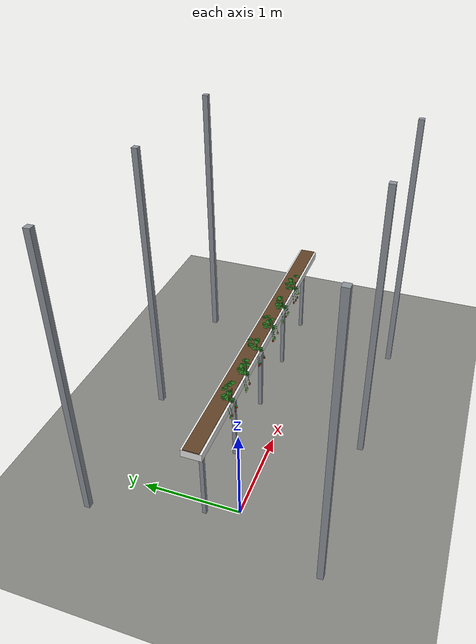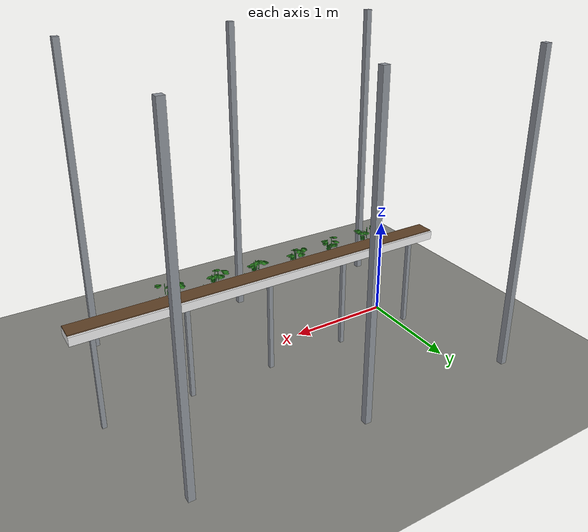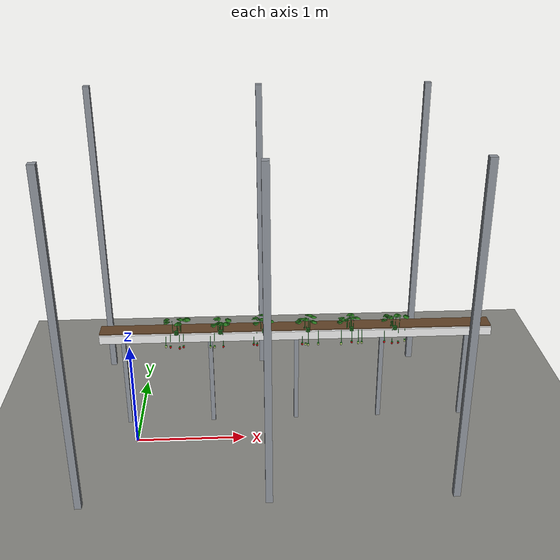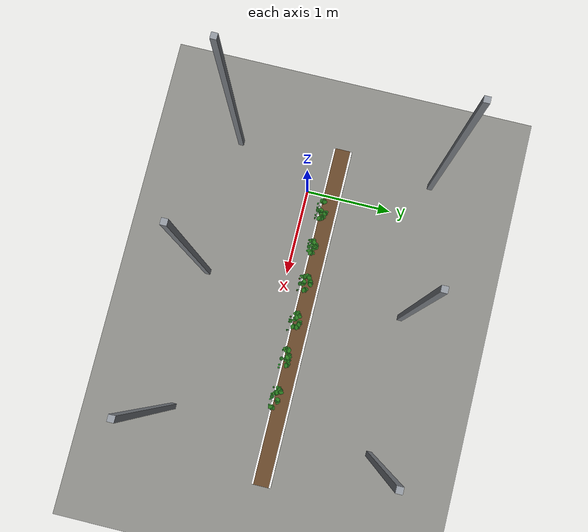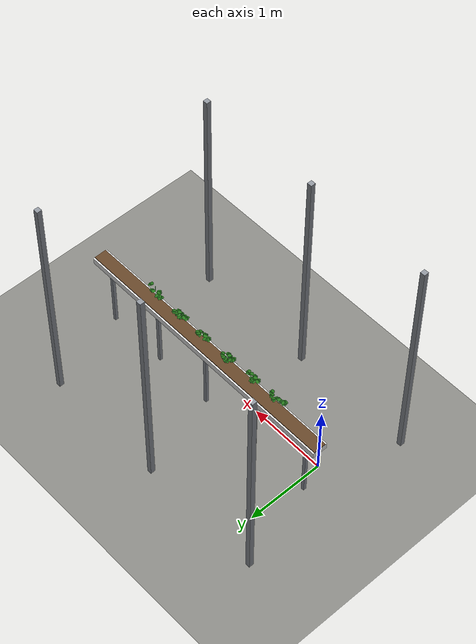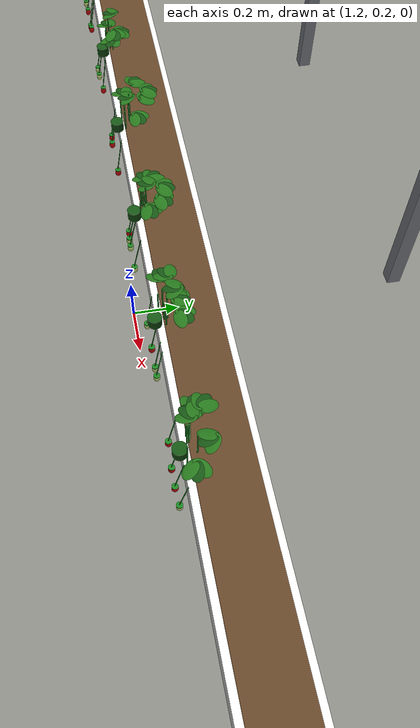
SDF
<?xml version="1.0"?>
<!-- Generated by tools/generate_worlds.py - edit the generator, not this file. -->
<sdf version="1.8">
<world name="strawberry_greenhouse">
  <physics name="1ms" type="ignored">
    <max_step_size>0.001</max_step_size>
    <real_time_factor>1.0</real_time_factor>
  </physics>
  <plugin filename="ignition-gazebo-physics-system" name="ignition::gazebo::systems::Physics"/>
  <plugin filename="ignition-gazebo-user-commands-system" name="ignition::gazebo::systems::UserCommands"/>
  <plugin filename="ignition-gazebo-scene-broadcaster-system" name="ignition::gazebo::systems::SceneBroadcaster"/>
  <plugin filename="ignition-gazebo-sensors-system" name="ignition::gazebo::systems::Sensors">
    <render_engine>ogre2</render_engine>
  </plugin>
  <gravity>0 0 -9.81</gravity>
  <scene>
    <ambient>0.55 0.55 0.55 1</ambient>
    <background>0.72 0.82 0.92 1</background>
    <shadows>true</shadows>
  </scene>
  <light type="directional" name="sun">
    <cast_shadows>true</cast_shadows>
    <pose>0 0 10 0 0 0</pose>
    <diffuse>0.85 0.85 0.82 1</diffuse>
    <specular>0.2 0.2 0.2 1</specular>
    <direction>-0.3 0.4 -0.9</direction>
  </light>
  <light type="directional" name="greenhouse_diffuse">
    <cast_shadows>false</cast_shadows>
    <pose>0 0 10 0 0 0</pose>
    <diffuse>0.35 0.35 0.35 1</diffuse>
    <specular>0 0 0 1</specular>
    <direction>0.2 -0.5 -0.8</direction>
  </light>
  <model name="floor">
    <static>true</static>
    <link name="link">
      <collision name="c_collision"><geometry><plane><normal>0 0 1</normal><size>20 20</size></plane></geometry><surface><friction><ode><mu>1.0</mu><mu2>1.0</mu2></ode></friction></surface></collision>
      <visual name="v"><geometry><plane><normal>0 0 1</normal><size>20 20</size></plane></geometry><material><ambient>0.520 0.520 0.500 1</ambient><diffuse>0.520 0.520 0.500 1</diffuse><specular>0.1 0.1 0.1 1</specular></material></visual>
    </link>
  </model>

<model name="post_0a"><static>true</static><pose>-0.4000 -0.9000 1.5000 0.0000 0.0000 0.0000</pose><link name="link"><visual name="v"><geometry><box><size>0.0600 0.0600 3.0000</size></box></geometry><material><ambient>0.550 0.570 0.600 1</ambient><diffuse>0.550 0.570 0.600 1</diffuse><specular>0.1 0.1 0.1 1</specular></material></visual></link></model>
<model name="post_0b"><static>true</static><pose>-0.4000 1.4000 1.5000 0.0000 0.0000 0.0000</pose><link name="link"><visual name="v"><geometry><box><size>0.0600 0.0600 3.0000</size></box></geometry><material><ambient>0.550 0.570 0.600 1</ambient><diffuse>0.550 0.570 0.600 1</diffuse><specular>0.1 0.1 0.1 1</specular></material></visual></link></model>
<model name="post_1a"><static>true</static><pose>1.2000 -0.9000 1.5000 0.0000 0.0000 0.0000</pose><link name="link"><visual name="v"><geometry><box><size>0.0600 0.0600 3.0000</size></box></geometry><material><ambient>0.550 0.570 0.600 1</ambient><diffuse>0.550 0.570 0.600 1</diffuse><specular>0.1 0.1 0.1 1</specular></material></visual></link></model>
<model name="post_1b"><static>true</static><pose>1.2000 1.4000 1.5000 0.0000 0.0000 0.0000</pose><link name="link"><visual name="v"><geometry><box><size>0.0600 0.0600 3.0000</size></box></geometry><material><ambient>0.550 0.570 0.600 1</ambient><diffuse>0.550 0.570 0.600 1</diffuse><specular>0.1 0.1 0.1 1</specular></material></visual></link></model>
<model name="post_2a"><static>true</static><pose>2.8000 -0.9000 1.5000 0.0000 0.0000 0.0000</pose><link name="link"><visual name="v"><geometry><box><size>0.0600 0.0600 3.0000</size></box></geometry><material><ambient>0.550 0.570 0.600 1</ambient><diffuse>0.550 0.570 0.600 1</diffuse><specular>0.1 0.1 0.1 1</specular></material></visual></link></model>
<model name="post_2b"><static>true</static><pose>2.8000 1.4000 1.5000 0.0000 0.0000 0.0000</pose><link name="link"><visual name="v"><geometry><box><size>0.0600 0.0600 3.0000</size></box></geometry><material><ambient>0.550 0.570 0.600 1</ambient><diffuse>0.550 0.570 0.600 1</diffuse><specular>0.1 0.1 0.1 1</specular></material></visual></link></model>
<model name="gutter"><static>true</static><pose>1.5000 0.3150 0.9600 0.0000 0.0000 0.0000</pose><link name="link"><visual name="gutter"><geometry><box><size>3.6000 0.2000 0.0800</size></box></geometry><material><ambient>0.920 0.920 0.920 1</ambient><diffuse>0.920 0.920 0.920 1</diffuse><specular>0.1 0.1 0.1 1</specular></material></visual><collision name="gutter_collision"><geometry><box><size>3.6000 0.2000 0.0800</size></box></geometry><surface><friction><ode><mu>1.0</mu><mu2>1.0</mu2></ode></friction></surface></collision><visual name="substrate"><pose>0.0000 0.0000 0.0450 0.0000 0.0000 0.0000</pose><geometry><box><size>3.6000 0.1600 0.0100</size></box></geometry><material><ambient>0.380 0.260 0.150 1</ambient><diffuse>0.380 0.260 0.150 1</diffuse><specular>0.1 0.1 0.1 1</specular></material></visual><visual name="leg_0"><pose>-1.6000 0.0000 -0.5000 0.0000 0.0000 0.0000</pose><geometry><box><size>0.0400 0.0400 0.9200</size></box></geometry><material><ambient>0.550 0.570 0.600 1</ambient><diffuse>0.550 0.570 0.600 1</diffuse><specular>0.1 0.1 0.1 1</specular></material></visual><visual name="leg_1"><pose>-0.8000 0.0000 -0.5000 0.0000 0.0000 0.0000</pose><geometry><box><size>0.0400 0.0400 0.9200</size></box></geometry><material><ambient>0.550 0.570 0.600 1</ambient><diffuse>0.550 0.570 0.600 1</diffuse><specular>0.1 0.1 0.1 1</specular></material></visual><visual name="leg_2"><pose>0.0000 0.0000 -0.5000 0.0000 0.0000 0.0000</pose><geometry><box><size>0.0400 0.0400 0.9200</size></box></geometry><material><ambient>0.550 0.570 0.600 1</ambient><diffuse>0.550 0.570 0.600 1</diffuse><specular>0.1 0.1 0.1 1</specular></material></visual><visual name="leg_3"><pose>0.8000 0.0000 -0.5000 0.0000 0.0000 0.0000</pose><geometry><box><size>0.0400 0.0400 0.9200</size></box></geometry><material><ambient>0.550 0.570 0.600 1</ambient><diffuse>0.550 0.570 0.600 1</diffuse><specular>0.1 0.1 0.1 1</specular></material></visual><visual name="leg_4"><pose>1.6000 0.0000 -0.5000 0.0000 0.0000 0.0000</pose><geometry><box><size>0.0400 0.0400 0.9200</size></box></geometry><material><ambient>0.550 0.570 0.600 1</ambient><diffuse>0.550 0.570 0.600 1</diffuse><specular>0.1 0.1 0.1 1</specular></material></visual></link></model>
<model name="fruit_0"><pose>0.3030 0.1893 0.8920 0.0000 0.0000 0.0000</pose><link name="link"><inertial><mass>0.015</mass><inertia><ixx>1.171e-06</ixx><iyy>1.171e-06</iyy><izz>9.025e-07</izz><ixy>0</ixy><ixz>0</ixz><iyz>0</iyz></inertia></inertial><visual name="berry"><geometry><ellipsoid><radii>0.0095 0.0095 0.0120</radii></ellipsoid></geometry><material><ambient>0.720 0.820 0.450 1</ambient><diffuse>0.720 0.820 0.450 1</diffuse><specular>0.1 0.1 0.1 1</specular></material></visual><visual name="calyx"><pose>0.0000 0.0000 0.0120 0.0000 0.0000 0.0000</pose><geometry><cylinder><radius>0.0090</radius><length>0.0030</length></cylinder></geometry><material><ambient>0.100 0.500 0.120 1</ambient><diffuse>0.100 0.500 0.120 1</diffuse><specular>0.1 0.1 0.1 1</specular></material></visual><collision name="core_collision"><geometry><sphere><radius>0.0040</radius></sphere></geometry><surface><friction><ode><mu>1.0</mu><mu2>1.0</mu2></ode></friction></surface></collision></link><plugin filename="ignition-gazebo-detachable-joint-system" name="ignition::gazebo::systems::DetachableJoint"><parent_link>link</parent_link><child_model>agrobot</child_model><child_link>link_4</child_link><attach_topic>/agrobot/sim/fruit_0/attach_gripper</attach_topic><detach_topic>/agrobot/sim/fruit_0/detach_gripper</detach_topic><suppress_child_warning>true</suppress_child_warning></plugin></model>
<model name="fruit_1"><pose>0.3444 0.1916 0.8848 0.0000 0.0000 0.0000</pose><link name="link"><inertial><mass>0.015</mass><inertia><ixx>1.171e-06</ixx><iyy>1.171e-06</iyy><izz>9.025e-07</izz><ixy>0</ixy><ixz>0</ixz><iyz>0</iyz></inertia></inertial><visual name="berry"><geometry><ellipsoid><radii>0.0095 0.0095 0.0120</radii></ellipsoid></geometry><material><ambient>0.780 0.040 0.050 1</ambient><diffuse>0.780 0.040 0.050 1</diffuse><specular>0.1 0.1 0.1 1</specular><emissive>0.117 0.006 0.007 1</emissive></material></visual><visual name="calyx"><pose>0.0000 0.0000 0.0120 0.0000 0.0000 0.0000</pose><geometry><cylinder><radius>0.0090</radius><length>0.0030</length></cylinder></geometry><material><ambient>0.100 0.500 0.120 1</ambient><diffuse>0.100 0.500 0.120 1</diffuse><specular>0.1 0.1 0.1 1</specular></material></visual><collision name="core_collision"><geometry><sphere><radius>0.0040</radius></sphere></geometry><surface><friction><ode><mu>1.0</mu><mu2>1.0</mu2></ode></friction></surface></collision></link><plugin filename="ignition-gazebo-detachable-joint-system" name="ignition::gazebo::systems::DetachableJoint"><parent_link>link</parent_link><child_model>agrobot</child_model><child_link>link_4</child_link><attach_topic>/agrobot/sim/fruit_1/attach_gripper</attach_topic><detach_topic>/agrobot/sim/fruit_1/detach_gripper</detach_topic><suppress_child_warning>true</suppress_child_warning></plugin></model>
<model name="fruit_2"><pose>0.4257 0.1914 0.8701 0.0000 0.0000 0.0000</pose><link name="link"><inertial><mass>0.015</mass><inertia><ixx>1.171e-06</ixx><iyy>1.171e-06</iyy><izz>9.025e-07</izz><ixy>0</ixy><ixz>0</ixz><iyz>0</iyz></inertia></inertial><visual name="berry"><geometry><ellipsoid><radii>0.0095 0.0095 0.0120</radii></ellipsoid></geometry><material><ambient>0.780 0.040 0.050 1</ambient><diffuse>0.780 0.040 0.050 1</diffuse><specular>0.1 0.1 0.1 1</specular><emissive>0.117 0.006 0.007 1</emissive></material></visual><visual name="calyx"><pose>0.0000 0.0000 0.0120 0.0000 0.0000 0.0000</pose><geometry><cylinder><radius>0.0090</radius><length>0.0030</length></cylinder></geometry><material><ambient>0.100 0.500 0.120 1</ambient><diffuse>0.100 0.500 0.120 1</diffuse><specular>0.1 0.1 0.1 1</specular></material></visual><collision name="core_collision"><geometry><sphere><radius>0.0040</radius></sphere></geometry><surface><friction><ode><mu>1.0</mu><mu2>1.0</mu2></ode></friction></surface></collision></link><plugin filename="ignition-gazebo-detachable-joint-system" name="ignition::gazebo::systems::DetachableJoint"><parent_link>link</parent_link><child_model>agrobot</child_model><child_link>link_4</child_link><attach_topic>/agrobot/sim/fruit_2/attach_gripper</attach_topic><detach_topic>/agrobot/sim/fruit_2/detach_gripper</detach_topic><suppress_child_warning>true</suppress_child_warning></plugin></model>
<model name="fruit_3"><pose>0.4625 0.1923 0.8838 0.0000 0.0000 0.0000</pose><link name="link"><inertial><mass>0.015</mass><inertia><ixx>1.171e-06</ixx><iyy>1.171e-06</iyy><izz>9.025e-07</izz><ixy>0</ixy><ixz>0</ixz><iyz>0</iyz></inertia></inertial><visual name="berry"><geometry><ellipsoid><radii>0.0095 0.0095 0.0120</radii></ellipsoid></geometry><material><ambient>0.780 0.040 0.050 1</ambient><diffuse>0.780 0.040 0.050 1</diffuse><specular>0.1 0.1 0.1 1</specular><emissive>0.117 0.006 0.007 1</emissive></material></visual><visual name="calyx"><pose>0.0000 0.0000 0.0120 0.0000 0.0000 0.0000</pose><geometry><cylinder><radius>0.0090</radius><length>0.0030</length></cylinder></geometry><material><ambient>0.100 0.500 0.120 1</ambient><diffuse>0.100 0.500 0.120 1</diffuse><specular>0.1 0.1 0.1 1</specular></material></visual><collision name="core_collision"><geometry><sphere><radius>0.0040</radius></sphere></geometry><surface><friction><ode><mu>1.0</mu><mu2>1.0</mu2></ode></friction></surface></collision></link><plugin filename="ignition-gazebo-detachable-joint-system" name="ignition::gazebo::systems::DetachableJoint"><parent_link>link</parent_link><child_model>agrobot</child_model><child_link>link_4</child_link><attach_topic>/agrobot/sim/fruit_3/attach_gripper</attach_topic><detach_topic>/agrobot/sim/fruit_3/detach_gripper</detach_topic><suppress_child_warning>true</suppress_child_warning></plugin></model>
<model name="plant_0"><static>true</static><pose>0.4000 0.2100 1.0200 0.0000 0.0000 0.0000</pose><link name="crown"><inertial><mass>0.3</mass><inertia><ixx>1.250e-04</ixx><iyy>1.250e-04</iyy><izz>1.250e-04</izz><ixy>0</ixy><ixz>0</ixz><iyz>0</iyz></inertia></inertial><visual name="crown"><geometry><cylinder><radius>0.0200</radius><length>0.0300</length></cylinder></geometry><material><ambient>0.080 0.320 0.070 1</ambient><diffuse>0.080 0.320 0.070 1</diffuse><specular>0.1 0.1 0.1 1</specular></material></visual><visual name="petiole_0"><pose>-0.0325 0.0180 0.0573 0.0000 0.0000 0.0000</pose><geometry><cylinder><radius>0.0020</radius><length>0.1147</length></cylinder></geometry><material><ambient>0.100 0.500 0.120 1</ambient><diffuse>0.100 0.500 0.120 1</diffuse><specular>0.1 0.1 0.1 1</specular></material></visual><visual name="leaf_0_0"><pose>-0.0758 0.0529 0.1147 0.2000 0.1500 2.1424</pose><geometry><ellipsoid><radii>0.0280 0.0180 0.0030</radii></ellipsoid></geometry><material><ambient>0.140 0.450 0.100 1</ambient><diffuse>0.140 0.450 0.100 1</diffuse><specular>0.1 0.1 0.1 1</specular></material></visual><visual name="leaf_0_1"><pose>-0.0841 0.0419 0.1147 0.2000 0.1500 2.8424</pose><geometry><ellipsoid><radii>0.0280 0.0180 0.0030</radii></ellipsoid></geometry><material><ambient>0.080 0.320 0.070 1</ambient><diffuse>0.080 0.320 0.070 1</diffuse><specular>0.1 0.1 0.1 1</specular></material></visual><visual name="leaf_0_2"><pose>-0.0834 0.0282 0.1147 0.2000 0.1500 3.5424</pose><geometry><ellipsoid><radii>0.0280 0.0180 0.0030</radii></ellipsoid></geometry><material><ambient>0.140 0.450 0.100 1</ambient><diffuse>0.140 0.450 0.100 1</diffuse><specular>0.1 0.1 0.1 1</specular></material></visual><visual name="petiole_1"><pose>-0.0319 0.0156 0.0456 0.0000 0.0000 0.0000</pose><geometry><cylinder><radius>0.0020</radius><length>0.0911</length></cylinder></geometry><material><ambient>0.100 0.500 0.120 1</ambient><diffuse>0.100 0.500 0.120 1</diffuse><specular>0.1 0.1 0.1 1</specular></material></visual><visual name="leaf_1_0"><pose>-0.0761 0.0471 0.0911 0.2000 0.1500 2.2258</pose><geometry><ellipsoid><radii>0.0280 0.0180 0.0030</radii></ellipsoid></geometry><material><ambient>0.140 0.450 0.100 1</ambient><diffuse>0.140 0.450 0.100 1</diffuse><specular>0.1 0.1 0.1 1</specular></material></visual><visual name="leaf_1_1"><pose>-0.0834 0.0355 0.0911 0.2000 0.1500 2.9258</pose><geometry><ellipsoid><radii>0.0280 0.0180 0.0030</radii></ellipsoid></geometry><material><ambient>0.080 0.320 0.070 1</ambient><diffuse>0.080 0.320 0.070 1</diffuse><specular>0.1 0.1 0.1 1</specular></material></visual><visual name="leaf_1_2"><pose>-0.0816 0.0219 0.0911 0.2000 0.1500 3.6258</pose><geometry><ellipsoid><radii>0.0280 0.0180 0.0030</radii></ellipsoid></geometry><material><ambient>0.140 0.450 0.100 1</ambient><diffuse>0.140 0.450 0.100 1</diffuse><specular>0.1 0.1 0.1 1</specular></material></visual><visual name="petiole_2"><pose>0.0131 0.0341 0.0470 0.0000 0.0000 0.0000</pose><geometry><cylinder><radius>0.0020</radius><length>0.0941</length></cylinder></geometry><material><ambient>0.100 0.500 0.120 1</ambient><diffuse>0.100 0.500 0.120 1</diffuse><specular>0.1 0.1 0.1 1</specular></material></visual><visual name="leaf_2_0"><pose>0.0441 0.0770 0.0941 0.2000 0.1500 0.4603</pose><geometry><ellipsoid><radii>0.0280 0.0180 0.0030</radii></ellipsoid></geometry><material><ambient>0.140 0.450 0.100 1</ambient><diffuse>0.140 0.450 0.100 1</diffuse><specular>0.1 0.1 0.1 1</specular></material></visual><visual name="leaf_2_1"><pose>0.0342 0.0865 0.0941 0.2000 0.1500 1.1603</pose><geometry><ellipsoid><radii>0.0280 0.0180 0.0030</radii></ellipsoid></geometry><material><ambient>0.080 0.320 0.070 1</ambient><diffuse>0.080 0.320 0.070 1</diffuse><specular>0.1 0.1 0.1 1</specular></material></visual><visual name="leaf_2_2"><pose>0.0205 0.0873 0.0941 0.2000 0.1500 1.8603</pose><geometry><ellipsoid><radii>0.0280 0.0180 0.0030</radii></ellipsoid></geometry><material><ambient>0.140 0.450 0.100 1</ambient><diffuse>0.140 0.450 0.100 1</diffuse><specular>0.1 0.1 0.1 1</specular></material></visual><visual name="petiole_3"><pose>0.0060 0.0272 0.0356 0.0000 0.0000 0.0000</pose><geometry><cylinder><radius>0.0020</radius><length>0.0712</length></cylinder></geometry><material><ambient>0.100 0.500 0.120 1</ambient><diffuse>0.100 0.500 0.120 1</diffuse><specular>0.1 0.1 0.1 1</specular></material></visual><visual name="leaf_3_0"><pose>0.0036 0.0363 0.0712 0.2000 0.1500 4.2824</pose><geometry><ellipsoid><radii>0.0280 0.0180 0.0030</radii></ellipsoid></geometry><material><ambient>0.140 0.450 0.100 1</ambient><diffuse>0.140 0.450 0.100 1</diffuse><specular>0.1 0.1 0.1 1</specular></material></visual><visual name="leaf_3_1"><pose>0.0173 0.0352 0.0712 0.2000 0.1500 4.9824</pose><geometry><ellipsoid><radii>0.0280 0.0180 0.0030</radii></ellipsoid></geometry><material><ambient>0.080 0.320 0.070 1</ambient><diffuse>0.080 0.320 0.070 1</diffuse><specular>0.1 0.1 0.1 1</specular></material></visual><visual name="leaf_3_2"><pose>0.0284 0.0432 0.0712 0.2000 0.1500 5.6824</pose><geometry><ellipsoid><radii>0.0280 0.0180 0.0030</radii></ellipsoid></geometry><material><ambient>0.140 0.450 0.100 1</ambient><diffuse>0.140 0.450 0.100 1</diffuse><specular>0.1 0.1 0.1 1</specular></material></visual><visual name="petiole_4"><pose>0.0339 0.0274 0.0493 0.0000 0.0000 0.0000</pose><geometry><cylinder><radius>0.0020</radius><length>0.0985</length></cylinder></geometry><material><ambient>0.100 0.500 0.120 1</ambient><diffuse>0.100 0.500 0.120 1</diffuse><specular>0.1 0.1 0.1 1</specular></material></visual><visual name="leaf_4_0"><pose>0.0876 0.0521 0.0985 0.2000 0.1500 -0.1303</pose><geometry><ellipsoid><radii>0.0280 0.0180 0.0030</radii></ellipsoid></geometry><material><ambient>0.140 0.450 0.100 1</ambient><diffuse>0.140 0.450 0.100 1</diffuse><specular>0.1 0.1 0.1 1</specular></material></visual><visual name="leaf_4_1"><pose>0.0846 0.0655 0.0985 0.2000 0.1500 0.5697</pose><geometry><ellipsoid><radii>0.0280 0.0180 0.0030</radii></ellipsoid></geometry><material><ambient>0.080 0.320 0.070 1</ambient><diffuse>0.080 0.320 0.070 1</diffuse><specular>0.1 0.1 0.1 1</specular></material></visual><visual name="leaf_4_2"><pose>0.0737 0.0738 0.0985 0.2000 0.1500 1.2697</pose><geometry><ellipsoid><radii>0.0280 0.0180 0.0030</radii></ellipsoid></geometry><material><ambient>0.140 0.450 0.100 1</ambient><diffuse>0.140 0.450 0.100 1</diffuse><specular>0.1 0.1 0.1 1</specular></material></visual><visual name="petiole_5"><pose>0.0430 0.0193 0.0588 0.0000 0.0000 0.0000</pose><geometry><cylinder><radius>0.0020</radius><length>0.1175</length></cylinder></geometry><material><ambient>0.100 0.500 0.120 1</ambient><diffuse>0.100 0.500 0.120 1</diffuse><specular>0.1 0.1 0.1 1</specular></material></visual><visual name="leaf_5_0"><pose>0.1042 0.0301 0.1175 0.2000 0.1500 -0.4369</pose><geometry><ellipsoid><radii>0.0280 0.0180 0.0030</radii></ellipsoid></geometry><material><ambient>0.140 0.450 0.100 1</ambient><diffuse>0.140 0.450 0.100 1</diffuse><specular>0.1 0.1 0.1 1</specular></material></visual><visual name="leaf_5_1"><pose>0.1054 0.0437 0.1175 0.2000 0.1500 0.2631</pose><geometry><ellipsoid><radii>0.0280 0.0180 0.0030</radii></ellipsoid></geometry><material><ambient>0.080 0.320 0.070 1</ambient><diffuse>0.080 0.320 0.070 1</diffuse><specular>0.1 0.1 0.1 1</specular></material></visual><visual name="leaf_5_2"><pose>0.0975 0.0550 0.1175 0.2000 0.1500 0.9631</pose><geometry><ellipsoid><radii>0.0280 0.0180 0.0030</radii></ellipsoid></geometry><material><ambient>0.140 0.450 0.100 1</ambient><diffuse>0.140 0.450 0.100 1</diffuse><specular>0.1 0.1 0.1 1</specular></material></visual><visual name="peduncle_fruit_0"><pose>-0.0970 -0.0079 -0.0635 -0.2591 0.0000 0.0000</pose><geometry><cylinder><radius>0.0015</radius><length>0.1004</length></cylinder></geometry><material><ambient>0.100 0.500 0.120 1</ambient><diffuse>0.100 0.500 0.120 1</diffuse><specular>0.1 0.1 0.1 1</specular></material></visual><visual name="peduncle_fruit_1"><pose>-0.0556 -0.0067 -0.0671 -0.2208 0.0000 0.0000</pose><geometry><cylinder><radius>0.0015</radius><length>0.1068</length></cylinder></geometry><material><ambient>0.100 0.500 0.120 1</ambient><diffuse>0.100 0.500 0.120 1</diffuse><specular>0.1 0.1 0.1 1</specular></material></visual><visual name="peduncle_fruit_2"><pose>0.0257 -0.0068 -0.0744 -0.1963 0.0000 0.0000</pose><geometry><cylinder><radius>0.0015</radius><length>0.1212</length></cylinder></geometry><material><ambient>0.100 0.500 0.120 1</ambient><diffuse>0.100 0.500 0.120 1</diffuse><specular>0.1 0.1 0.1 1</specular></material></visual><visual name="peduncle_fruit_3"><pose>0.0625 -0.0064 -0.0676 -0.2129 0.0000 0.0000</pose><geometry><cylinder><radius>0.0015</radius><length>0.1076</length></cylinder></geometry><material><ambient>0.100 0.500 0.120 1</ambient><diffuse>0.100 0.500 0.120 1</diffuse><specular>0.1 0.1 0.1 1</specular></material></visual></link><plugin filename="ignition-gazebo-detachable-joint-system" name="ignition::gazebo::systems::DetachableJoint"><parent_link>crown</parent_link><child_model>fruit_0</child_model><child_link>link</child_link><detach_topic>/agrobot/sim/fruit_0/detach_anchor</detach_topic></plugin><plugin filename="ignition-gazebo-detachable-joint-system" name="ignition::gazebo::systems::DetachableJoint"><parent_link>crown</parent_link><child_model>fruit_1</child_model><child_link>link</child_link><detach_topic>/agrobot/sim/fruit_1/detach_anchor</detach_topic></plugin><plugin filename="ignition-gazebo-detachable-joint-system" name="ignition::gazebo::systems::DetachableJoint"><parent_link>crown</parent_link><child_model>fruit_2</child_model><child_link>link</child_link><detach_topic>/agrobot/sim/fruit_2/detach_anchor</detach_topic></plugin><plugin filename="ignition-gazebo-detachable-joint-system" name="ignition::gazebo::systems::DetachableJoint"><parent_link>crown</parent_link><child_model>fruit_3</child_model><child_link>link</child_link><detach_topic>/agrobot/sim/fruit_3/detach_anchor</detach_topic></plugin></model>
<model name="fruit_4"><pose>0.7063 0.1897 0.8783 0.0000 0.0000 0.0000</pose><link name="link"><inertial><mass>0.015</mass><inertia><ixx>1.171e-06</ixx><iyy>1.171e-06</iyy><izz>9.025e-07</izz><ixy>0</ixy><ixz>0</ixz><iyz>0</iyz></inertia></inertial><visual name="berry"><geometry><ellipsoid><radii>0.0095 0.0095 0.0120</radii></ellipsoid></geometry><material><ambient>0.720 0.820 0.450 1</ambient><diffuse>0.720 0.820 0.450 1</diffuse><specular>0.1 0.1 0.1 1</specular></material></visual><visual name="calyx"><pose>0.0000 0.0000 0.0120 0.0000 0.0000 0.0000</pose><geometry><cylinder><radius>0.0090</radius><length>0.0030</length></cylinder></geometry><material><ambient>0.100 0.500 0.120 1</ambient><diffuse>0.100 0.500 0.120 1</diffuse><specular>0.1 0.1 0.1 1</specular></material></visual><collision name="core_collision"><geometry><sphere><radius>0.0040</radius></sphere></geometry><surface><friction><ode><mu>1.0</mu><mu2>1.0</mu2></ode></friction></surface></collision></link><plugin filename="ignition-gazebo-detachable-joint-system" name="ignition::gazebo::systems::DetachableJoint"><parent_link>link</parent_link><child_model>agrobot</child_model><child_link>link_4</child_link><attach_topic>/agrobot/sim/fruit_4/attach_gripper</attach_topic><detach_topic>/agrobot/sim/fruit_4/detach_gripper</detach_topic><suppress_child_warning>true</suppress_child_warning></plugin></model>
<model name="fruit_5"><pose>0.7441 0.1899 0.8762 0.0000 0.0000 0.0000</pose><link name="link"><inertial><mass>0.015</mass><inertia><ixx>1.171e-06</ixx><iyy>1.171e-06</iyy><izz>9.025e-07</izz><ixy>0</ixy><ixz>0</ixz><iyz>0</iyz></inertia></inertial><visual name="berry"><geometry><ellipsoid><radii>0.0095 0.0095 0.0120</radii></ellipsoid></geometry><material><ambient>0.720 0.820 0.450 1</ambient><diffuse>0.720 0.820 0.450 1</diffuse><specular>0.1 0.1 0.1 1</specular></material></visual><visual name="calyx"><pose>0.0000 0.0000 0.0120 0.0000 0.0000 0.0000</pose><geometry><cylinder><radius>0.0090</radius><length>0.0030</length></cylinder></geometry><material><ambient>0.100 0.500 0.120 1</ambient><diffuse>0.100 0.500 0.120 1</diffuse><specular>0.1 0.1 0.1 1</specular></material></visual><collision name="core_collision"><geometry><sphere><radius>0.0040</radius></sphere></geometry><surface><friction><ode><mu>1.0</mu><mu2>1.0</mu2></ode></friction></surface></collision></link><plugin filename="ignition-gazebo-detachable-joint-system" name="ignition::gazebo::systems::DetachableJoint"><parent_link>link</parent_link><child_model>agrobot</child_model><child_link>link_4</child_link><attach_topic>/agrobot/sim/fruit_5/attach_gripper</attach_topic><detach_topic>/agrobot/sim/fruit_5/detach_gripper</detach_topic><suppress_child_warning>true</suppress_child_warning></plugin></model>
<model name="fruit_6"><pose>0.8230 0.1954 0.8744 0.0000 0.0000 0.0000</pose><link name="link"><inertial><mass>0.015</mass><inertia><ixx>1.171e-06</ixx><iyy>1.171e-06</iyy><izz>9.025e-07</izz><ixy>0</ixy><ixz>0</ixz><iyz>0</iyz></inertia></inertial><visual name="berry"><geometry><ellipsoid><radii>0.0095 0.0095 0.0120</radii></ellipsoid></geometry><material><ambient>0.780 0.040 0.050 1</ambient><diffuse>0.780 0.040 0.050 1</diffuse><specular>0.1 0.1 0.1 1</specular><emissive>0.117 0.006 0.007 1</emissive></material></visual><visual name="calyx"><pose>0.0000 0.0000 0.0120 0.0000 0.0000 0.0000</pose><geometry><cylinder><radius>0.0090</radius><length>0.0030</length></cylinder></geometry><material><ambient>0.100 0.500 0.120 1</ambient><diffuse>0.100 0.500 0.120 1</diffuse><specular>0.1 0.1 0.1 1</specular></material></visual><collision name="core_collision"><geometry><sphere><radius>0.0040</radius></sphere></geometry><surface><friction><ode><mu>1.0</mu><mu2>1.0</mu2></ode></friction></surface></collision></link><plugin filename="ignition-gazebo-detachable-joint-system" name="ignition::gazebo::systems::DetachableJoint"><parent_link>link</parent_link><child_model>agrobot</child_model><child_link>link_4</child_link><attach_topic>/agrobot/sim/fruit_6/attach_gripper</attach_topic><detach_topic>/agrobot/sim/fruit_6/detach_gripper</detach_topic><suppress_child_warning>true</suppress_child_warning></plugin></model>
<model name="plant_1"><static>true</static><pose>0.8000 0.2100 1.0200 0.0000 0.0000 0.0000</pose><link name="crown"><inertial><mass>0.3</mass><inertia><ixx>1.250e-04</ixx><iyy>1.250e-04</iyy><izz>1.250e-04</izz><ixy>0</ixy><ixz>0</ixz><iyz>0</iyz></inertia></inertial><visual name="crown"><geometry><cylinder><radius>0.0200</radius><length>0.0300</length></cylinder></geometry><material><ambient>0.080 0.320 0.070 1</ambient><diffuse>0.080 0.320 0.070 1</diffuse><specular>0.1 0.1 0.1 1</specular></material></visual><visual name="petiole_0"><pose>0.0201 0.0174 0.0339 0.0000 0.0000 0.0000</pose><geometry><cylinder><radius>0.0020</radius><length>0.0678</length></cylinder></geometry><material><ambient>0.100 0.500 0.120 1</ambient><diffuse>0.100 0.500 0.120 1</diffuse><specular>0.1 0.1 0.1 1</specular></material></visual><visual name="leaf_0_0"><pose>0.0487 0.0166 0.0678 0.2000 0.1500 5.1540</pose><geometry><ellipsoid><radii>0.0280 0.0180 0.0030</radii></ellipsoid></geometry><material><ambient>0.140 0.450 0.100 1</ambient><diffuse>0.140 0.450 0.100 1</diffuse><specular>0.1 0.1 0.1 1</specular></material></visual><visual name="leaf_0_1"><pose>0.0583 0.0264 0.0678 0.2000 0.1500 5.8540</pose><geometry><ellipsoid><radii>0.0280 0.0180 0.0030</radii></ellipsoid></geometry><material><ambient>0.080 0.320 0.070 1</ambient><diffuse>0.080 0.320 0.070 1</diffuse><specular>0.1 0.1 0.1 1</specular></material></visual><visual name="leaf_0_2"><pose>0.0594 0.0401 0.0678 0.2000 0.1500 6.5540</pose><geometry><ellipsoid><radii>0.0280 0.0180 0.0030</radii></ellipsoid></geometry><material><ambient>0.140 0.450 0.100 1</ambient><diffuse>0.140 0.450 0.100 1</diffuse><specular>0.1 0.1 0.1 1</specular></material></visual><visual name="petiole_1"><pose>0.0016 0.0362 0.0260 0.0000 0.0000 0.0000</pose><geometry><cylinder><radius>0.0020</radius><length>0.0521</length></cylinder></geometry><material><ambient>0.100 0.500 0.120 1</ambient><diffuse>0.100 0.500 0.120 1</diffuse><specular>0.1 0.1 0.1 1</specular></material></visual><visual name="leaf_1_0"><pose>-0.0088 0.0565 0.0521 0.2000 0.1500 4.0626</pose><geometry><ellipsoid><radii>0.0280 0.0180 0.0030</radii></ellipsoid></geometry><material><ambient>0.140 0.450 0.100 1</ambient><diffuse>0.140 0.450 0.100 1</diffuse><specular>0.1 0.1 0.1 1</specular></material></visual><visual name="leaf_1_1"><pose>0.0043 0.0525 0.0521 0.2000 0.1500 4.7626</pose><geometry><ellipsoid><radii>0.0280 0.0180 0.0030</radii></ellipsoid></geometry><material><ambient>0.080 0.320 0.070 1</ambient><diffuse>0.080 0.320 0.070 1</diffuse><specular>0.1 0.1 0.1 1</specular></material></visual><visual name="leaf_1_2"><pose>0.0169 0.0578 0.0521 0.2000 0.1500 5.4626</pose><geometry><ellipsoid><radii>0.0280 0.0180 0.0030</radii></ellipsoid></geometry><material><ambient>0.140 0.450 0.100 1</ambient><diffuse>0.140 0.450 0.100 1</diffuse><specular>0.1 0.1 0.1 1</specular></material></visual><visual name="petiole_2"><pose>-0.0209 0.0170 0.0288 0.0000 0.0000 0.0000</pose><geometry><cylinder><radius>0.0020</radius><length>0.0575</length></cylinder></geometry><material><ambient>0.100 0.500 0.120 1</ambient><diffuse>0.100 0.500 0.120 1</diffuse><specular>0.1 0.1 0.1 1</specular></material></visual><visual name="leaf_2_0"><pose>-0.0610 0.0400 0.0575 0.2000 0.1500 2.8383</pose><geometry><ellipsoid><radii>0.0280 0.0180 0.0030</radii></ellipsoid></geometry><material><ambient>0.140 0.450 0.100 1</ambient><diffuse>0.140 0.450 0.100 1</diffuse><specular>0.1 0.1 0.1 1</specular></material></visual><visual name="leaf_2_1"><pose>-0.0603 0.0263 0.0575 0.2000 0.1500 3.5383</pose><geometry><ellipsoid><radii>0.0280 0.0180 0.0030</radii></ellipsoid></geometry><material><ambient>0.080 0.320 0.070 1</ambient><diffuse>0.080 0.320 0.070 1</diffuse><specular>0.1 0.1 0.1 1</specular></material></visual><visual name="leaf_2_2"><pose>-0.0510 0.0162 0.0575 0.2000 0.1500 4.2383</pose><geometry><ellipsoid><radii>0.0280 0.0180 0.0030</radii></ellipsoid></geometry><material><ambient>0.140 0.450 0.100 1</ambient><diffuse>0.140 0.450 0.100 1</diffuse><specular>0.1 0.1 0.1 1</specular></material></visual><visual name="petiole_3"><pose>-0.0055 0.0268 0.0256 0.0000 0.0000 0.0000</pose><geometry><cylinder><radius>0.0020</radius><length>0.0512</length></cylinder></geometry><material><ambient>0.100 0.500 0.120 1</ambient><diffuse>0.100 0.500 0.120 1</diffuse><specular>0.1 0.1 0.1 1</specular></material></visual><visual name="leaf_3_0"><pose>-0.0024 0.0716 0.0512 0.2000 0.1500 1.1278</pose><geometry><ellipsoid><radii>0.0280 0.0180 0.0030</radii></ellipsoid></geometry><material><ambient>0.140 0.450 0.100 1</ambient><diffuse>0.140 0.450 0.100 1</diffuse><specular>0.1 0.1 0.1 1</specular></material></visual><visual name="leaf_3_1"><pose>-0.0161 0.0729 0.0512 0.2000 0.1500 1.8278</pose><geometry><ellipsoid><radii>0.0280 0.0180 0.0030</radii></ellipsoid></geometry><material><ambient>0.080 0.320 0.070 1</ambient><diffuse>0.080 0.320 0.070 1</diffuse><specular>0.1 0.1 0.1 1</specular></material></visual><visual name="leaf_3_2"><pose>-0.0274 0.0651 0.0512 0.2000 0.1500 2.5278</pose><geometry><ellipsoid><radii>0.0280 0.0180 0.0030</radii></ellipsoid></geometry><material><ambient>0.140 0.450 0.100 1</ambient><diffuse>0.140 0.450 0.100 1</diffuse><specular>0.1 0.1 0.1 1</specular></material></visual><visual name="petiole_4"><pose>-0.0101 0.0286 0.0574 0.0000 0.0000 0.0000</pose><geometry><cylinder><radius>0.0020</radius><length>0.1149</length></cylinder></geometry><material><ambient>0.100 0.500 0.120 1</ambient><diffuse>0.100 0.500 0.120 1</diffuse><specular>0.1 0.1 0.1 1</specular></material></visual><visual name="leaf_4_0"><pose>-0.0381 0.0483 0.1149 0.2000 0.1500 3.6033</pose><geometry><ellipsoid><radii>0.0280 0.0180 0.0030</radii></ellipsoid></geometry><material><ambient>0.140 0.450 0.100 1</ambient><diffuse>0.140 0.450 0.100 1</diffuse><specular>0.1 0.1 0.1 1</specular></material></visual><visual name="leaf_4_1"><pose>-0.0281 0.0388 0.1149 0.2000 0.1500 4.3033</pose><geometry><ellipsoid><radii>0.0280 0.0180 0.0030</radii></ellipsoid></geometry><material><ambient>0.080 0.320 0.070 1</ambient><diffuse>0.080 0.320 0.070 1</diffuse><specular>0.1 0.1 0.1 1</specular></material></visual><visual name="leaf_4_2"><pose>-0.0144 0.0380 0.1149 0.2000 0.1500 5.0033</pose><geometry><ellipsoid><radii>0.0280 0.0180 0.0030</radii></ellipsoid></geometry><material><ambient>0.140 0.450 0.100 1</ambient><diffuse>0.140 0.450 0.100 1</diffuse><specular>0.1 0.1 0.1 1</specular></material></visual><visual name="petiole_5"><pose>0.0278 0.0176 0.0498 0.0000 0.0000 0.0000</pose><geometry><cylinder><radius>0.0020</radius><length>0.0996</length></cylinder></geometry><material><ambient>0.100 0.500 0.120 1</ambient><diffuse>0.100 0.500 0.120 1</diffuse><specular>0.1 0.1 0.1 1</specular></material></visual><visual name="leaf_5_0"><pose>0.0743 0.0279 0.0996 0.2000 0.1500 -0.3712</pose><geometry><ellipsoid><radii>0.0280 0.0180 0.0030</radii></ellipsoid></geometry><material><ambient>0.140 0.450 0.100 1</ambient><diffuse>0.140 0.450 0.100 1</diffuse><specular>0.1 0.1 0.1 1</specular></material></visual><visual name="leaf_5_1"><pose>0.0746 0.0416 0.0996 0.2000 0.1500 0.3288</pose><geometry><ellipsoid><radii>0.0280 0.0180 0.0030</radii></ellipsoid></geometry><material><ambient>0.080 0.320 0.070 1</ambient><diffuse>0.080 0.320 0.070 1</diffuse><specular>0.1 0.1 0.1 1</specular></material></visual><visual name="leaf_5_2"><pose>0.0659 0.0523 0.0996 0.2000 0.1500 1.0288</pose><geometry><ellipsoid><radii>0.0280 0.0180 0.0030</radii></ellipsoid></geometry><material><ambient>0.140 0.450 0.100 1</ambient><diffuse>0.140 0.450 0.100 1</diffuse><specular>0.1 0.1 0.1 1</specular></material></visual><visual name="peduncle_fruit_4"><pose>-0.0937 -0.0077 -0.0703 -0.2247 0.0000 0.0000</pose><geometry><cylinder><radius>0.0015</radius><length>0.1135</length></cylinder></geometry><material><ambient>0.100 0.500 0.120 1</ambient><diffuse>0.100 0.500 0.120 1</diffuse><specular>0.1 0.1 0.1 1</specular></material></visual><visual name="peduncle_fruit_5"><pose>-0.0559 -0.0075 -0.0714 -0.2185 0.0000 0.0000</pose><geometry><cylinder><radius>0.0015</radius><length>0.1156</length></cylinder></geometry><material><ambient>0.100 0.500 0.120 1</ambient><diffuse>0.100 0.500 0.120 1</diffuse><specular>0.1 0.1 0.1 1</specular></material></visual><visual name="peduncle_fruit_6"><pose>0.0230 -0.0048 -0.0723 -0.1697 0.0000 0.0000</pose><geometry><cylinder><radius>0.0015</radius><length>0.1162</length></cylinder></geometry><material><ambient>0.100 0.500 0.120 1</ambient><diffuse>0.100 0.500 0.120 1</diffuse><specular>0.1 0.1 0.1 1</specular></material></visual></link><plugin filename="ignition-gazebo-detachable-joint-system" name="ignition::gazebo::systems::DetachableJoint"><parent_link>crown</parent_link><child_model>fruit_4</child_model><child_link>link</child_link><detach_topic>/agrobot/sim/fruit_4/detach_anchor</detach_topic></plugin><plugin filename="ignition-gazebo-detachable-joint-system" name="ignition::gazebo::systems::DetachableJoint"><parent_link>crown</parent_link><child_model>fruit_5</child_model><child_link>link</child_link><detach_topic>/agrobot/sim/fruit_5/detach_anchor</detach_topic></plugin><plugin filename="ignition-gazebo-detachable-joint-system" name="ignition::gazebo::systems::DetachableJoint"><parent_link>crown</parent_link><child_model>fruit_6</child_model><child_link>link</child_link><detach_topic>/agrobot/sim/fruit_6/detach_anchor</detach_topic></plugin></model>
<model name="fruit_7"><pose>1.1022 0.1939 0.8908 0.0000 0.0000 0.0000</pose><link name="link"><inertial><mass>0.015</mass><inertia><ixx>1.171e-06</ixx><iyy>1.171e-06</iyy><izz>9.025e-07</izz><ixy>0</ixy><ixz>0</ixz><iyz>0</iyz></inertia></inertial><visual name="berry"><geometry><ellipsoid><radii>0.0095 0.0095 0.0120</radii></ellipsoid></geometry><material><ambient>0.780 0.040 0.050 1</ambient><diffuse>0.780 0.040 0.050 1</diffuse><specular>0.1 0.1 0.1 1</specular><emissive>0.117 0.006 0.007 1</emissive></material></visual><visual name="calyx"><pose>0.0000 0.0000 0.0120 0.0000 0.0000 0.0000</pose><geometry><cylinder><radius>0.0090</radius><length>0.0030</length></cylinder></geometry><material><ambient>0.100 0.500 0.120 1</ambient><diffuse>0.100 0.500 0.120 1</diffuse><specular>0.1 0.1 0.1 1</specular></material></visual><collision name="core_collision"><geometry><sphere><radius>0.0040</radius></sphere></geometry><surface><friction><ode><mu>1.0</mu><mu2>1.0</mu2></ode></friction></surface></collision></link><plugin filename="ignition-gazebo-detachable-joint-system" name="ignition::gazebo::systems::DetachableJoint"><parent_link>link</parent_link><child_model>agrobot</child_model><child_link>link_4</child_link><attach_topic>/agrobot/sim/fruit_7/attach_gripper</attach_topic><detach_topic>/agrobot/sim/fruit_7/detach_gripper</detach_topic><suppress_child_warning>true</suppress_child_warning></plugin></model>
<model name="fruit_8"><pose>1.1332 0.1907 0.8859 0.0000 0.0000 0.0000</pose><link name="link"><inertial><mass>0.015</mass><inertia><ixx>1.171e-06</ixx><iyy>1.171e-06</iyy><izz>9.025e-07</izz><ixy>0</ixy><ixz>0</ixz><iyz>0</iyz></inertia></inertial><visual name="berry"><geometry><ellipsoid><radii>0.0095 0.0095 0.0120</radii></ellipsoid></geometry><material><ambient>0.780 0.040 0.050 1</ambient><diffuse>0.780 0.040 0.050 1</diffuse><specular>0.1 0.1 0.1 1</specular><emissive>0.117 0.006 0.007 1</emissive></material></visual><visual name="calyx"><pose>0.0000 0.0000 0.0120 0.0000 0.0000 0.0000</pose><geometry><cylinder><radius>0.0090</radius><length>0.0030</length></cylinder></geometry><material><ambient>0.100 0.500 0.120 1</ambient><diffuse>0.100 0.500 0.120 1</diffuse><specular>0.1 0.1 0.1 1</specular></material></visual><collision name="core_collision"><geometry><sphere><radius>0.0040</radius></sphere></geometry><surface><friction><ode><mu>1.0</mu><mu2>1.0</mu2></ode></friction></surface></collision></link><plugin filename="ignition-gazebo-detachable-joint-system" name="ignition::gazebo::systems::DetachableJoint"><parent_link>link</parent_link><child_model>agrobot</child_model><child_link>link_4</child_link><attach_topic>/agrobot/sim/fruit_8/attach_gripper</attach_topic><detach_topic>/agrobot/sim/fruit_8/detach_gripper</detach_topic><suppress_child_warning>true</suppress_child_warning></plugin></model>
<model name="fruit_9"><pose>1.2579 0.1940 0.8732 0.0000 0.0000 0.0000</pose><link name="link"><inertial><mass>0.015</mass><inertia><ixx>1.171e-06</ixx><iyy>1.171e-06</iyy><izz>9.025e-07</izz><ixy>0</ixy><ixz>0</ixz><iyz>0</iyz></inertia></inertial><visual name="berry"><geometry><ellipsoid><radii>0.0095 0.0095 0.0120</radii></ellipsoid></geometry><material><ambient>0.780 0.040 0.050 1</ambient><diffuse>0.780 0.040 0.050 1</diffuse><specular>0.1 0.1 0.1 1</specular><emissive>0.117 0.006 0.007 1</emissive></material></visual><visual name="calyx"><pose>0.0000 0.0000 0.0120 0.0000 0.0000 0.0000</pose><geometry><cylinder><radius>0.0090</radius><length>0.0030</length></cylinder></geometry><material><ambient>0.100 0.500 0.120 1</ambient><diffuse>0.100 0.500 0.120 1</diffuse><specular>0.1 0.1 0.1 1</specular></material></visual><collision name="core_collision"><geometry><sphere><radius>0.0040</radius></sphere></geometry><surface><friction><ode><mu>1.0</mu><mu2>1.0</mu2></ode></friction></surface></collision></link><plugin filename="ignition-gazebo-detachable-joint-system" name="ignition::gazebo::systems::DetachableJoint"><parent_link>link</parent_link><child_model>agrobot</child_model><child_link>link_4</child_link><attach_topic>/agrobot/sim/fruit_9/attach_gripper</attach_topic><detach_topic>/agrobot/sim/fruit_9/detach_gripper</detach_topic><suppress_child_warning>true</suppress_child_warning></plugin></model>
<model name="plant_2"><static>true</static><pose>1.2000 0.2100 1.0200 0.0000 0.0000 0.0000</pose><link name="crown"><inertial><mass>0.3</mass><inertia><ixx>1.250e-04</ixx><iyy>1.250e-04</iyy><izz>1.250e-04</izz><ixy>0</ixy><ixz>0</ixz><iyz>0</iyz></inertia></inertial><visual name="crown"><geometry><cylinder><radius>0.0200</radius><length>0.0300</length></cylinder></geometry><material><ambient>0.080 0.320 0.070 1</ambient><diffuse>0.080 0.320 0.070 1</diffuse><specular>0.1 0.1 0.1 1</specular></material></visual><visual name="petiole_0"><pose>-0.0290 0.0191 0.0317 0.0000 0.0000 0.0000</pose><geometry><cylinder><radius>0.0020</radius><length>0.0633</length></cylinder></geometry><material><ambient>0.100 0.500 0.120 1</ambient><diffuse>0.100 0.500 0.120 1</diffuse><specular>0.1 0.1 0.1 1</specular></material></visual><visual name="leaf_0_0"><pose>-0.0770 0.0446 0.0633 0.2000 0.1500 2.8142</pose><geometry><ellipsoid><radii>0.0280 0.0180 0.0030</radii></ellipsoid></geometry><material><ambient>0.140 0.450 0.100 1</ambient><diffuse>0.140 0.450 0.100 1</diffuse><specular>0.1 0.1 0.1 1</specular></material></visual><visual name="leaf_0_1"><pose>-0.0767 0.0309 0.0633 0.2000 0.1500 3.5142</pose><geometry><ellipsoid><radii>0.0280 0.0180 0.0030</radii></ellipsoid></geometry><material><ambient>0.080 0.320 0.070 1</ambient><diffuse>0.080 0.320 0.070 1</diffuse><specular>0.1 0.1 0.1 1</specular></material></visual><visual name="leaf_0_2"><pose>-0.0676 0.0206 0.0633 0.2000 0.1500 4.2142</pose><geometry><ellipsoid><radii>0.0280 0.0180 0.0030</radii></ellipsoid></geometry><material><ambient>0.140 0.450 0.100 1</ambient><diffuse>0.140 0.450 0.100 1</diffuse><specular>0.1 0.1 0.1 1</specular></material></visual><visual name="petiole_1"><pose>-0.0026 0.0285 0.0475 0.0000 0.0000 0.0000</pose><geometry><cylinder><radius>0.0020</radius><length>0.0951</length></cylinder></geometry><material><ambient>0.100 0.500 0.120 1</ambient><diffuse>0.100 0.500 0.120 1</diffuse><specular>0.1 0.1 0.1 1</specular></material></visual><visual name="leaf_1_0"><pose>-0.0198 0.0433 0.0951 0.2000 0.1500 3.8986</pose><geometry><ellipsoid><radii>0.0280 0.0180 0.0030</radii></ellipsoid></geometry><material><ambient>0.140 0.450 0.100 1</ambient><diffuse>0.140 0.450 0.100 1</diffuse><specular>0.1 0.1 0.1 1</specular></material></visual><visual name="leaf_1_1"><pose>-0.0076 0.0371 0.0951 0.2000 0.1500 4.5986</pose><geometry><ellipsoid><radii>0.0280 0.0180 0.0030</radii></ellipsoid></geometry><material><ambient>0.080 0.320 0.070 1</ambient><diffuse>0.080 0.320 0.070 1</diffuse><specular>0.1 0.1 0.1 1</specular></material></visual><visual name="leaf_1_2"><pose>0.0058 0.0403 0.0951 0.2000 0.1500 5.2986</pose><geometry><ellipsoid><radii>0.0280 0.0180 0.0030</radii></ellipsoid></geometry><material><ambient>0.140 0.450 0.100 1</ambient><diffuse>0.140 0.450 0.100 1</diffuse><specular>0.1 0.1 0.1 1</specular></material></visual><visual name="petiole_2"><pose>0.0227 0.0263 0.0325 0.0000 0.0000 0.0000</pose><geometry><cylinder><radius>0.0020</radius><length>0.0649</length></cylinder></geometry><material><ambient>0.100 0.500 0.120 1</ambient><diffuse>0.100 0.500 0.120 1</diffuse><specular>0.1 0.1 0.1 1</specular></material></visual><visual name="leaf_2_0"><pose>0.0654 0.0533 0.0649 0.2000 0.1500 0.0320</pose><geometry><ellipsoid><radii>0.0280 0.0180 0.0030</radii></ellipsoid></geometry><material><ambient>0.140 0.450 0.100 1</ambient><diffuse>0.140 0.450 0.100 1</diffuse><specular>0.1 0.1 0.1 1</specular></material></visual><visual name="leaf_2_1"><pose>0.0603 0.0660 0.0649 0.2000 0.1500 0.7320</pose><geometry><ellipsoid><radii>0.0280 0.0180 0.0030</radii></ellipsoid></geometry><material><ambient>0.080 0.320 0.070 1</ambient><diffuse>0.080 0.320 0.070 1</diffuse><specular>0.1 0.1 0.1 1</specular></material></visual><visual name="leaf_2_2"><pose>0.0482 0.0724 0.0649 0.2000 0.1500 1.4320</pose><geometry><ellipsoid><radii>0.0280 0.0180 0.0030</radii></ellipsoid></geometry><material><ambient>0.140 0.450 0.100 1</ambient><diffuse>0.140 0.450 0.100 1</diffuse><specular>0.1 0.1 0.1 1</specular></material></visual><visual name="petiole_3"><pose>-0.0055 0.0451 0.0531 0.0000 0.0000 0.0000</pose><geometry><cylinder><radius>0.0020</radius><length>0.1062</length></cylinder></geometry><material><ambient>0.100 0.500 0.120 1</ambient><diffuse>0.100 0.500 0.120 1</diffuse><specular>0.1 0.1 0.1 1</specular></material></visual><visual name="leaf_3_0"><pose>-0.0001 0.1071 0.1062 0.2000 0.1500 0.9952</pose><geometry><ellipsoid><radii>0.0280 0.0180 0.0030</radii></ellipsoid></geometry><material><ambient>0.140 0.450 0.100 1</ambient><diffuse>0.140 0.450 0.100 1</diffuse><specular>0.1 0.1 0.1 1</specular></material></visual><visual name="leaf_3_1"><pose>-0.0135 0.1101 0.1062 0.2000 0.1500 1.6952</pose><geometry><ellipsoid><radii>0.0280 0.0180 0.0030</radii></ellipsoid></geometry><material><ambient>0.080 0.320 0.070 1</ambient><diffuse>0.080 0.320 0.070 1</diffuse><specular>0.1 0.1 0.1 1</specular></material></visual><visual name="leaf_3_2"><pose>-0.0257 0.1039 0.1062 0.2000 0.1500 2.3952</pose><geometry><ellipsoid><radii>0.0280 0.0180 0.0030</radii></ellipsoid></geometry><material><ambient>0.140 0.450 0.100 1</ambient><diffuse>0.140 0.450 0.100 1</diffuse><specular>0.1 0.1 0.1 1</specular></material></visual><visual name="petiole_4"><pose>-0.0141 0.0418 0.0324 0.0000 0.0000 0.0000</pose><geometry><cylinder><radius>0.0020</radius><length>0.0647</length></cylinder></geometry><material><ambient>0.100 0.500 0.120 1</ambient><diffuse>0.100 0.500 0.120 1</diffuse><specular>0.1 0.1 0.1 1</specular></material></visual><visual name="leaf_4_0"><pose>-0.0211 0.1023 0.0647 0.2000 0.1500 1.2110</pose><geometry><ellipsoid><radii>0.0280 0.0180 0.0030</radii></ellipsoid></geometry><material><ambient>0.140 0.450 0.100 1</ambient><diffuse>0.140 0.450 0.100 1</diffuse><specular>0.1 0.1 0.1 1</specular></material></visual><visual name="leaf_4_1"><pose>-0.0348 0.1024 0.0647 0.2000 0.1500 1.9110</pose><geometry><ellipsoid><radii>0.0280 0.0180 0.0030</radii></ellipsoid></geometry><material><ambient>0.080 0.320 0.070 1</ambient><diffuse>0.080 0.320 0.070 1</diffuse><specular>0.1 0.1 0.1 1</specular></material></visual><visual name="leaf_4_2"><pose>-0.0454 0.0937 0.0647 0.2000 0.1500 2.6110</pose><geometry><ellipsoid><radii>0.0280 0.0180 0.0030</radii></ellipsoid></geometry><material><ambient>0.140 0.450 0.100 1</ambient><diffuse>0.140 0.450 0.100 1</diffuse><specular>0.1 0.1 0.1 1</specular></material></visual><visual name="petiole_5"><pose>-0.0326 0.0304 0.0475 0.0000 0.0000 0.0000</pose><geometry><cylinder><radius>0.0020</radius><length>0.0949</length></cylinder></geometry><material><ambient>0.100 0.500 0.120 1</ambient><diffuse>0.100 0.500 0.120 1</diffuse><specular>0.1 0.1 0.1 1</specular></material></visual><visual name="leaf_5_0"><pose>-0.0692 0.0804 0.0949 0.2000 0.1500 1.7773</pose><geometry><ellipsoid><radii>0.0280 0.0180 0.0030</radii></ellipsoid></geometry><material><ambient>0.140 0.450 0.100 1</ambient><diffuse>0.140 0.450 0.100 1</diffuse><specular>0.1 0.1 0.1 1</specular></material></visual><visual name="leaf_5_1"><pose>-0.0809 0.0731 0.0949 0.2000 0.1500 2.4773</pose><geometry><ellipsoid><radii>0.0280 0.0180 0.0030</radii></ellipsoid></geometry><material><ambient>0.080 0.320 0.070 1</ambient><diffuse>0.080 0.320 0.070 1</diffuse><specular>0.1 0.1 0.1 1</specular></material></visual><visual name="leaf_5_2"><pose>-0.0851 0.0601 0.0949 0.2000 0.1500 3.1773</pose><geometry><ellipsoid><radii>0.0280 0.0180 0.0030</radii></ellipsoid></geometry><material><ambient>0.140 0.450 0.100 1</ambient><diffuse>0.140 0.450 0.100 1</diffuse><specular>0.1 0.1 0.1 1</specular></material></visual><visual name="peduncle_fruit_7"><pose>-0.0978 -0.0056 -0.0641 -0.2117 0.0000 0.0000</pose><geometry><cylinder><radius>0.0015</radius><length>0.1005</length></cylinder></geometry><material><ambient>0.100 0.500 0.120 1</ambient><diffuse>0.100 0.500 0.120 1</diffuse><specular>0.1 0.1 0.1 1</specular></material></visual><visual name="peduncle_fruit_8"><pose>-0.0668 -0.0072 -0.0665 -0.2318 0.0000 0.0000</pose><geometry><cylinder><radius>0.0015</radius><length>0.1059</length></cylinder></geometry><material><ambient>0.100 0.500 0.120 1</ambient><diffuse>0.100 0.500 0.120 1</diffuse><specular>0.1 0.1 0.1 1</specular></material></visual><visual name="peduncle_fruit_9"><pose>0.0579 -0.0055 -0.0729 -0.1796 0.0000 0.0000</pose><geometry><cylinder><radius>0.0015</radius><length>0.1177</length></cylinder></geometry><material><ambient>0.100 0.500 0.120 1</ambient><diffuse>0.100 0.500 0.120 1</diffuse><specular>0.1 0.1 0.1 1</specular></material></visual></link><plugin filename="ignition-gazebo-detachable-joint-system" name="ignition::gazebo::systems::DetachableJoint"><parent_link>crown</parent_link><child_model>fruit_7</child_model><child_link>link</child_link><detach_topic>/agrobot/sim/fruit_7/detach_anchor</detach_topic></plugin><plugin filename="ignition-gazebo-detachable-joint-system" name="ignition::gazebo::systems::DetachableJoint"><parent_link>crown</parent_link><child_model>fruit_8</child_model><child_link>link</child_link><detach_topic>/agrobot/sim/fruit_8/detach_anchor</detach_topic></plugin><plugin filename="ignition-gazebo-detachable-joint-system" name="ignition::gazebo::systems::DetachableJoint"><parent_link>crown</parent_link><child_model>fruit_9</child_model><child_link>link</child_link><detach_topic>/agrobot/sim/fruit_9/detach_anchor</detach_topic></plugin></model>
<model name="fruit_10"><pose>1.5465 0.1929 0.8830 0.0000 0.0000 0.0000</pose><link name="link"><inertial><mass>0.015</mass><inertia><ixx>1.171e-06</ixx><iyy>1.171e-06</iyy><izz>9.025e-07</izz><ixy>0</ixy><ixz>0</ixz><iyz>0</iyz></inertia></inertial><visual name="berry"><geometry><ellipsoid><radii>0.0095 0.0095 0.0120</radii></ellipsoid></geometry><material><ambient>0.780 0.040 0.050 1</ambient><diffuse>0.780 0.040 0.050 1</diffuse><specular>0.1 0.1 0.1 1</specular><emissive>0.117 0.006 0.007 1</emissive></material></visual><visual name="calyx"><pose>0.0000 0.0000 0.0120 0.0000 0.0000 0.0000</pose><geometry><cylinder><radius>0.0090</radius><length>0.0030</length></cylinder></geometry><material><ambient>0.100 0.500 0.120 1</ambient><diffuse>0.100 0.500 0.120 1</diffuse><specular>0.1 0.1 0.1 1</specular></material></visual><collision name="core_collision"><geometry><sphere><radius>0.0040</radius></sphere></geometry><surface><friction><ode><mu>1.0</mu><mu2>1.0</mu2></ode></friction></surface></collision></link><plugin filename="ignition-gazebo-detachable-joint-system" name="ignition::gazebo::systems::DetachableJoint"><parent_link>link</parent_link><child_model>agrobot</child_model><child_link>link_4</child_link><attach_topic>/agrobot/sim/fruit_10/attach_gripper</attach_topic><detach_topic>/agrobot/sim/fruit_10/detach_gripper</detach_topic><suppress_child_warning>true</suppress_child_warning></plugin></model>
<model name="fruit_11"><pose>1.5776 0.1900 0.8820 0.0000 0.0000 0.0000</pose><link name="link"><inertial><mass>0.015</mass><inertia><ixx>1.171e-06</ixx><iyy>1.171e-06</iyy><izz>9.025e-07</izz><ixy>0</ixy><ixz>0</ixz><iyz>0</iyz></inertia></inertial><visual name="berry"><geometry><ellipsoid><radii>0.0095 0.0095 0.0120</radii></ellipsoid></geometry><material><ambient>0.720 0.820 0.450 1</ambient><diffuse>0.720 0.820 0.450 1</diffuse><specular>0.1 0.1 0.1 1</specular></material></visual><visual name="calyx"><pose>0.0000 0.0000 0.0120 0.0000 0.0000 0.0000</pose><geometry><cylinder><radius>0.0090</radius><length>0.0030</length></cylinder></geometry><material><ambient>0.100 0.500 0.120 1</ambient><diffuse>0.100 0.500 0.120 1</diffuse><specular>0.1 0.1 0.1 1</specular></material></visual><collision name="core_collision"><geometry><sphere><radius>0.0040</radius></sphere></geometry><surface><friction><ode><mu>1.0</mu><mu2>1.0</mu2></ode></friction></surface></collision></link><plugin filename="ignition-gazebo-detachable-joint-system" name="ignition::gazebo::systems::DetachableJoint"><parent_link>link</parent_link><child_model>agrobot</child_model><child_link>link_4</child_link><attach_topic>/agrobot/sim/fruit_11/attach_gripper</attach_topic><detach_topic>/agrobot/sim/fruit_11/detach_gripper</detach_topic><suppress_child_warning>true</suppress_child_warning></plugin></model>
<model name="fruit_12"><pose>1.6019 0.1896 0.8753 0.0000 0.0000 0.0000</pose><link name="link"><inertial><mass>0.015</mass><inertia><ixx>1.171e-06</ixx><iyy>1.171e-06</iyy><izz>9.025e-07</izz><ixy>0</ixy><ixz>0</ixz><iyz>0</iyz></inertia></inertial><visual name="berry"><geometry><ellipsoid><radii>0.0095 0.0095 0.0120</radii></ellipsoid></geometry><material><ambient>0.720 0.820 0.450 1</ambient><diffuse>0.720 0.820 0.450 1</diffuse><specular>0.1 0.1 0.1 1</specular></material></visual><visual name="calyx"><pose>0.0000 0.0000 0.0120 0.0000 0.0000 0.0000</pose><geometry><cylinder><radius>0.0090</radius><length>0.0030</length></cylinder></geometry><material><ambient>0.100 0.500 0.120 1</ambient><diffuse>0.100 0.500 0.120 1</diffuse><specular>0.1 0.1 0.1 1</specular></material></visual><collision name="core_collision"><geometry><sphere><radius>0.0040</radius></sphere></geometry><surface><friction><ode><mu>1.0</mu><mu2>1.0</mu2></ode></friction></surface></collision></link><plugin filename="ignition-gazebo-detachable-joint-system" name="ignition::gazebo::systems::DetachableJoint"><parent_link>link</parent_link><child_model>agrobot</child_model><child_link>link_4</child_link><attach_topic>/agrobot/sim/fruit_12/attach_gripper</attach_topic><detach_topic>/agrobot/sim/fruit_12/detach_gripper</detach_topic><suppress_child_warning>true</suppress_child_warning></plugin></model>
<model name="fruit_13"><pose>1.6940 0.1896 0.8803 0.0000 0.0000 0.0000</pose><link name="link"><inertial><mass>0.015</mass><inertia><ixx>1.171e-06</ixx><iyy>1.171e-06</iyy><izz>9.025e-07</izz><ixy>0</ixy><ixz>0</ixz><iyz>0</iyz></inertia></inertial><visual name="berry"><geometry><ellipsoid><radii>0.0095 0.0095 0.0120</radii></ellipsoid></geometry><material><ambient>0.720 0.820 0.450 1</ambient><diffuse>0.720 0.820 0.450 1</diffuse><specular>0.1 0.1 0.1 1</specular></material></visual><visual name="calyx"><pose>0.0000 0.0000 0.0120 0.0000 0.0000 0.0000</pose><geometry><cylinder><radius>0.0090</radius><length>0.0030</length></cylinder></geometry><material><ambient>0.100 0.500 0.120 1</ambient><diffuse>0.100 0.500 0.120 1</diffuse><specular>0.1 0.1 0.1 1</specular></material></visual><collision name="core_collision"><geometry><sphere><radius>0.0040</radius></sphere></geometry><surface><friction><ode><mu>1.0</mu><mu2>1.0</mu2></ode></friction></surface></collision></link><plugin filename="ignition-gazebo-detachable-joint-system" name="ignition::gazebo::systems::DetachableJoint"><parent_link>link</parent_link><child_model>agrobot</child_model><child_link>link_4</child_link><attach_topic>/agrobot/sim/fruit_13/attach_gripper</attach_topic><detach_topic>/agrobot/sim/fruit_13/detach_gripper</detach_topic><suppress_child_warning>true</suppress_child_warning></plugin></model>
<model name="plant_3"><static>true</static><pose>1.6000 0.2100 1.0200 0.0000 0.0000 0.0000</pose><link name="crown"><inertial><mass>0.3</mass><inertia><ixx>1.250e-04</ixx><iyy>1.250e-04</iyy><izz>1.250e-04</izz><ixy>0</ixy><ixz>0</ixz><iyz>0</iyz></inertia></inertial><visual name="crown"><geometry><cylinder><radius>0.0200</radius><length>0.0300</length></cylinder></geometry><material><ambient>0.080 0.320 0.070 1</ambient><diffuse>0.080 0.320 0.070 1</diffuse><specular>0.1 0.1 0.1 1</specular></material></visual><visual name="petiole_0"><pose>-0.0348 0.0270 0.0298 0.0000 0.0000 0.0000</pose><geometry><cylinder><radius>0.0020</radius><length>0.0595</length></cylinder></geometry><material><ambient>0.100 0.500 0.120 1</ambient><diffuse>0.100 0.500 0.120 1</diffuse><specular>0.1 0.1 0.1 1</specular></material></visual><visual name="leaf_0_0"><pose>-0.0894 0.0571 0.0595 0.2000 0.1500 2.9899</pose><geometry><ellipsoid><radii>0.0280 0.0180 0.0030</radii></ellipsoid></geometry><material><ambient>0.140 0.450 0.100 1</ambient><diffuse>0.140 0.450 0.100 1</diffuse><specular>0.1 0.1 0.1 1</specular></material></visual><visual name="leaf_0_1"><pose>-0.0867 0.0436 0.0595 0.2000 0.1500 3.6899</pose><geometry><ellipsoid><radii>0.0280 0.0180 0.0030</radii></ellipsoid></geometry><material><ambient>0.080 0.320 0.070 1</ambient><diffuse>0.080 0.320 0.070 1</diffuse><specular>0.1 0.1 0.1 1</specular></material></visual><visual name="leaf_0_2"><pose>-0.0760 0.0351 0.0595 0.2000 0.1500 4.3899</pose><geometry><ellipsoid><radii>0.0280 0.0180 0.0030</radii></ellipsoid></geometry><material><ambient>0.140 0.450 0.100 1</ambient><diffuse>0.140 0.450 0.100 1</diffuse><specular>0.1 0.1 0.1 1</specular></material></visual><visual name="petiole_1"><pose>-0.0269 0.0287 0.0359 0.0000 0.0000 0.0000</pose><geometry><cylinder><radius>0.0020</radius><length>0.0718</length></cylinder></geometry><material><ambient>0.100 0.500 0.120 1</ambient><diffuse>0.100 0.500 0.120 1</diffuse><specular>0.1 0.1 0.1 1</specular></material></visual><visual name="leaf_1_0"><pose>-0.0569 0.0772 0.0718 0.2000 0.1500 1.7259</pose><geometry><ellipsoid><radii>0.0280 0.0180 0.0030</radii></ellipsoid></geometry><material><ambient>0.140 0.450 0.100 1</ambient><diffuse>0.140 0.450 0.100 1</diffuse><specular>0.1 0.1 0.1 1</specular></material></visual><visual name="leaf_1_1"><pose>-0.0689 0.0706 0.0718 0.2000 0.1500 2.4259</pose><geometry><ellipsoid><radii>0.0280 0.0180 0.0030</radii></ellipsoid></geometry><material><ambient>0.080 0.320 0.070 1</ambient><diffuse>0.080 0.320 0.070 1</diffuse><specular>0.1 0.1 0.1 1</specular></material></visual><visual name="leaf_1_2"><pose>-0.0739 0.0578 0.0718 0.2000 0.1500 3.1259</pose><geometry><ellipsoid><radii>0.0280 0.0180 0.0030</radii></ellipsoid></geometry><material><ambient>0.140 0.450 0.100 1</ambient><diffuse>0.140 0.450 0.100 1</diffuse><specular>0.1 0.1 0.1 1</specular></material></visual><visual name="petiole_2"><pose>0.0048 0.0379 0.0504 0.0000 0.0000 0.0000</pose><geometry><cylinder><radius>0.0020</radius><length>0.1008</length></cylinder></geometry><material><ambient>0.100 0.500 0.120 1</ambient><diffuse>0.100 0.500 0.120 1</diffuse><specular>0.1 0.1 0.1 1</specular></material></visual><visual name="leaf_2_0"><pose>0.0244 0.0893 0.1008 0.2000 0.1500 0.7350</pose><geometry><ellipsoid><radii>0.0280 0.0180 0.0030</radii></ellipsoid></geometry><material><ambient>0.140 0.450 0.100 1</ambient><diffuse>0.140 0.450 0.100 1</diffuse><specular>0.1 0.1 0.1 1</specular></material></visual><visual name="leaf_2_1"><pose>0.0123 0.0957 0.1008 0.2000 0.1500 1.4350</pose><geometry><ellipsoid><radii>0.0280 0.0180 0.0030</radii></ellipsoid></geometry><material><ambient>0.080 0.320 0.070 1</ambient><diffuse>0.080 0.320 0.070 1</diffuse><specular>0.1 0.1 0.1 1</specular></material></visual><visual name="leaf_2_2"><pose>-0.0011 0.0928 0.1008 0.2000 0.1500 2.1350</pose><geometry><ellipsoid><radii>0.0280 0.0180 0.0030</radii></ellipsoid></geometry><material><ambient>0.140 0.450 0.100 1</ambient><diffuse>0.140 0.450 0.100 1</diffuse><specular>0.1 0.1 0.1 1</specular></material></visual><visual name="petiole_3"><pose>0.0194 0.0340 0.0444 0.0000 0.0000 0.0000</pose><geometry><cylinder><radius>0.0020</radius><length>0.0888</length></cylinder></geometry><material><ambient>0.100 0.500 0.120 1</ambient><diffuse>0.100 0.500 0.120 1</diffuse><specular>0.1 0.1 0.1 1</specular></material></visual><visual name="leaf_3_0"><pose>0.0580 0.0738 0.0888 0.2000 0.1500 0.2957</pose><geometry><ellipsoid><radii>0.0280 0.0180 0.0030</radii></ellipsoid></geometry><material><ambient>0.140 0.450 0.100 1</ambient><diffuse>0.140 0.450 0.100 1</diffuse><specular>0.1 0.1 0.1 1</specular></material></visual><visual name="leaf_3_1"><pose>0.0497 0.0847 0.0888 0.2000 0.1500 0.9957</pose><geometry><ellipsoid><radii>0.0280 0.0180 0.0030</radii></ellipsoid></geometry><material><ambient>0.080 0.320 0.070 1</ambient><diffuse>0.080 0.320 0.070 1</diffuse><specular>0.1 0.1 0.1 1</specular></material></visual><visual name="leaf_3_2"><pose>0.0364 0.0878 0.0888 0.2000 0.1500 1.6957</pose><geometry><ellipsoid><radii>0.0280 0.0180 0.0030</radii></ellipsoid></geometry><material><ambient>0.140 0.450 0.100 1</ambient><diffuse>0.140 0.450 0.100 1</diffuse><specular>0.1 0.1 0.1 1</specular></material></visual><visual name="petiole_4"><pose>-0.0115 0.0319 0.0419 0.0000 0.0000 0.0000</pose><geometry><cylinder><radius>0.0020</radius><length>0.0838</length></cylinder></geometry><material><ambient>0.100 0.500 0.120 1</ambient><diffuse>0.100 0.500 0.120 1</diffuse><specular>0.1 0.1 0.1 1</specular></material></visual><visual name="leaf_4_0"><pose>-0.0407 0.0547 0.0838 0.2000 0.1500 3.6164</pose><geometry><ellipsoid><radii>0.0280 0.0180 0.0030</radii></ellipsoid></geometry><material><ambient>0.140 0.450 0.100 1</ambient><diffuse>0.140 0.450 0.100 1</diffuse><specular>0.1 0.1 0.1 1</specular></material></visual><visual name="leaf_4_1"><pose>-0.0306 0.0454 0.0838 0.2000 0.1500 4.3164</pose><geometry><ellipsoid><radii>0.0280 0.0180 0.0030</radii></ellipsoid></geometry><material><ambient>0.080 0.320 0.070 1</ambient><diffuse>0.080 0.320 0.070 1</diffuse><specular>0.1 0.1 0.1 1</specular></material></visual><visual name="leaf_4_2"><pose>-0.0169 0.0448 0.0838 0.2000 0.1500 5.0164</pose><geometry><ellipsoid><radii>0.0280 0.0180 0.0030</radii></ellipsoid></geometry><material><ambient>0.140 0.450 0.100 1</ambient><diffuse>0.140 0.450 0.100 1</diffuse><specular>0.1 0.1 0.1 1</specular></material></visual><visual name="petiole_5"><pose>0.0187 0.0180 0.0288 0.0000 0.0000 0.0000</pose><geometry><cylinder><radius>0.0020</radius><length>0.0576</length></cylinder></geometry><material><ambient>0.100 0.500 0.120 1</ambient><diffuse>0.100 0.500 0.120 1</diffuse><specular>0.1 0.1 0.1 1</specular></material></visual><visual name="leaf_5_0"><pose>0.0569 0.0319 0.0576 0.2000 0.1500 -0.2068</pose><geometry><ellipsoid><radii>0.0280 0.0180 0.0030</radii></ellipsoid></geometry><material><ambient>0.140 0.450 0.100 1</ambient><diffuse>0.140 0.450 0.100 1</diffuse><specular>0.1 0.1 0.1 1</specular></material></visual><visual name="leaf_5_1"><pose>0.0549 0.0455 0.0576 0.2000 0.1500 0.4932</pose><geometry><ellipsoid><radii>0.0280 0.0180 0.0030</radii></ellipsoid></geometry><material><ambient>0.080 0.320 0.070 1</ambient><diffuse>0.080 0.320 0.070 1</diffuse><specular>0.1 0.1 0.1 1</specular></material></visual><visual name="leaf_5_2"><pose>0.0447 0.0546 0.0576 0.2000 0.1500 1.1932</pose><geometry><ellipsoid><radii>0.0280 0.0180 0.0030</radii></ellipsoid></geometry><material><ambient>0.140 0.450 0.100 1</ambient><diffuse>0.140 0.450 0.100 1</diffuse><specular>0.1 0.1 0.1 1</specular></material></visual><visual name="peduncle_fruit_10"><pose>-0.0535 -0.0060 -0.0680 -0.2053 0.0000 0.0000</pose><geometry><cylinder><radius>0.0015</radius><length>0.1083</length></cylinder></geometry><material><ambient>0.100 0.500 0.120 1</ambient><diffuse>0.100 0.500 0.120 1</diffuse><specular>0.1 0.1 0.1 1</specular></material></visual><visual name="peduncle_fruit_11"><pose>-0.0224 -0.0075 -0.0685 -0.2294 0.0000 0.0000</pose><geometry><cylinder><radius>0.0015</radius><length>0.1099</length></cylinder></geometry><material><ambient>0.100 0.500 0.120 1</ambient><diffuse>0.100 0.500 0.120 1</diffuse><specular>0.1 0.1 0.1 1</specular></material></visual><visual name="peduncle_fruit_12"><pose>0.0019 -0.0077 -0.0718 -0.2199 0.0000 0.0000</pose><geometry><cylinder><radius>0.0015</radius><length>0.1165</length></cylinder></geometry><material><ambient>0.100 0.500 0.120 1</ambient><diffuse>0.100 0.500 0.120 1</diffuse><specular>0.1 0.1 0.1 1</specular></material></visual><visual name="peduncle_fruit_13"><pose>0.0940 -0.0077 -0.0694 -0.2299 0.0000 0.0000</pose><geometry><cylinder><radius>0.0015</radius><length>0.1117</length></cylinder></geometry><material><ambient>0.100 0.500 0.120 1</ambient><diffuse>0.100 0.500 0.120 1</diffuse><specular>0.1 0.1 0.1 1</specular></material></visual></link><plugin filename="ignition-gazebo-detachable-joint-system" name="ignition::gazebo::systems::DetachableJoint"><parent_link>crown</parent_link><child_model>fruit_10</child_model><child_link>link</child_link><detach_topic>/agrobot/sim/fruit_10/detach_anchor</detach_topic></plugin><plugin filename="ignition-gazebo-detachable-joint-system" name="ignition::gazebo::systems::DetachableJoint"><parent_link>crown</parent_link><child_model>fruit_11</child_model><child_link>link</child_link><detach_topic>/agrobot/sim/fruit_11/detach_anchor</detach_topic></plugin><plugin filename="ignition-gazebo-detachable-joint-system" name="ignition::gazebo::systems::DetachableJoint"><parent_link>crown</parent_link><child_model>fruit_12</child_model><child_link>link</child_link><detach_topic>/agrobot/sim/fruit_12/detach_anchor</detach_topic></plugin><plugin filename="ignition-gazebo-detachable-joint-system" name="ignition::gazebo::systems::DetachableJoint"><parent_link>crown</parent_link><child_model>fruit_13</child_model><child_link>link</child_link><detach_topic>/agrobot/sim/fruit_13/detach_anchor</detach_topic></plugin></model>
<model name="fruit_14"><pose>1.9071 0.1970 0.8719 0.0000 0.0000 0.0000</pose><link name="link"><inertial><mass>0.015</mass><inertia><ixx>1.171e-06</ixx><iyy>1.171e-06</iyy><izz>9.025e-07</izz><ixy>0</ixy><ixz>0</ixz><iyz>0</iyz></inertia></inertial><visual name="berry"><geometry><ellipsoid><radii>0.0095 0.0095 0.0120</radii></ellipsoid></geometry><material><ambient>0.720 0.820 0.450 1</ambient><diffuse>0.720 0.820 0.450 1</diffuse><specular>0.1 0.1 0.1 1</specular></material></visual><visual name="calyx"><pose>0.0000 0.0000 0.0120 0.0000 0.0000 0.0000</pose><geometry><cylinder><radius>0.0090</radius><length>0.0030</length></cylinder></geometry><material><ambient>0.100 0.500 0.120 1</ambient><diffuse>0.100 0.500 0.120 1</diffuse><specular>0.1 0.1 0.1 1</specular></material></visual><collision name="core_collision"><geometry><sphere><radius>0.0040</radius></sphere></geometry><surface><friction><ode><mu>1.0</mu><mu2>1.0</mu2></ode></friction></surface></collision></link><plugin filename="ignition-gazebo-detachable-joint-system" name="ignition::gazebo::systems::DetachableJoint"><parent_link>link</parent_link><child_model>agrobot</child_model><child_link>link_4</child_link><attach_topic>/agrobot/sim/fruit_14/attach_gripper</attach_topic><detach_topic>/agrobot/sim/fruit_14/detach_gripper</detach_topic><suppress_child_warning>true</suppress_child_warning></plugin></model>
<model name="fruit_15"><pose>2.0038 0.1962 0.8884 0.0000 0.0000 0.0000</pose><link name="link"><inertial><mass>0.015</mass><inertia><ixx>1.171e-06</ixx><iyy>1.171e-06</iyy><izz>9.025e-07</izz><ixy>0</ixy><ixz>0</ixz><iyz>0</iyz></inertia></inertial><visual name="berry"><geometry><ellipsoid><radii>0.0095 0.0095 0.0120</radii></ellipsoid></geometry><material><ambient>0.780 0.040 0.050 1</ambient><diffuse>0.780 0.040 0.050 1</diffuse><specular>0.1 0.1 0.1 1</specular><emissive>0.117 0.006 0.007 1</emissive></material></visual><visual name="calyx"><pose>0.0000 0.0000 0.0120 0.0000 0.0000 0.0000</pose><geometry><cylinder><radius>0.0090</radius><length>0.0030</length></cylinder></geometry><material><ambient>0.100 0.500 0.120 1</ambient><diffuse>0.100 0.500 0.120 1</diffuse><specular>0.1 0.1 0.1 1</specular></material></visual><collision name="core_collision"><geometry><sphere><radius>0.0040</radius></sphere></geometry><surface><friction><ode><mu>1.0</mu><mu2>1.0</mu2></ode></friction></surface></collision></link><plugin filename="ignition-gazebo-detachable-joint-system" name="ignition::gazebo::systems::DetachableJoint"><parent_link>link</parent_link><child_model>agrobot</child_model><child_link>link_4</child_link><attach_topic>/agrobot/sim/fruit_15/attach_gripper</attach_topic><detach_topic>/agrobot/sim/fruit_15/detach_gripper</detach_topic><suppress_child_warning>true</suppress_child_warning></plugin></model>
<model name="fruit_16"><pose>2.0647 0.1963 0.8788 0.0000 0.0000 0.0000</pose><link name="link"><inertial><mass>0.015</mass><inertia><ixx>1.171e-06</ixx><iyy>1.171e-06</iyy><izz>9.025e-07</izz><ixy>0</ixy><ixz>0</ixz><iyz>0</iyz></inertia></inertial><visual name="berry"><geometry><ellipsoid><radii>0.0095 0.0095 0.0120</radii></ellipsoid></geometry><material><ambient>0.720 0.820 0.450 1</ambient><diffuse>0.720 0.820 0.450 1</diffuse><specular>0.1 0.1 0.1 1</specular></material></visual><visual name="calyx"><pose>0.0000 0.0000 0.0120 0.0000 0.0000 0.0000</pose><geometry><cylinder><radius>0.0090</radius><length>0.0030</length></cylinder></geometry><material><ambient>0.100 0.500 0.120 1</ambient><diffuse>0.100 0.500 0.120 1</diffuse><specular>0.1 0.1 0.1 1</specular></material></visual><collision name="core_collision"><geometry><sphere><radius>0.0040</radius></sphere></geometry><surface><friction><ode><mu>1.0</mu><mu2>1.0</mu2></ode></friction></surface></collision></link><plugin filename="ignition-gazebo-detachable-joint-system" name="ignition::gazebo::systems::DetachableJoint"><parent_link>link</parent_link><child_model>agrobot</child_model><child_link>link_4</child_link><attach_topic>/agrobot/sim/fruit_16/attach_gripper</attach_topic><detach_topic>/agrobot/sim/fruit_16/detach_gripper</detach_topic><suppress_child_warning>true</suppress_child_warning></plugin></model>
<model name="fruit_17"><pose>2.0964 0.1960 0.8804 0.0000 0.0000 0.0000</pose><link name="link"><inertial><mass>0.015</mass><inertia><ixx>1.171e-06</ixx><iyy>1.171e-06</iyy><izz>9.025e-07</izz><ixy>0</ixy><ixz>0</ixz><iyz>0</iyz></inertia></inertial><visual name="berry"><geometry><ellipsoid><radii>0.0095 0.0095 0.0120</radii></ellipsoid></geometry><material><ambient>0.720 0.820 0.450 1</ambient><diffuse>0.720 0.820 0.450 1</diffuse><specular>0.1 0.1 0.1 1</specular></material></visual><visual name="calyx"><pose>0.0000 0.0000 0.0120 0.0000 0.0000 0.0000</pose><geometry><cylinder><radius>0.0090</radius><length>0.0030</length></cylinder></geometry><material><ambient>0.100 0.500 0.120 1</ambient><diffuse>0.100 0.500 0.120 1</diffuse><specular>0.1 0.1 0.1 1</specular></material></visual><collision name="core_collision"><geometry><sphere><radius>0.0040</radius></sphere></geometry><surface><friction><ode><mu>1.0</mu><mu2>1.0</mu2></ode></friction></surface></collision></link><plugin filename="ignition-gazebo-detachable-joint-system" name="ignition::gazebo::systems::DetachableJoint"><parent_link>link</parent_link><child_model>agrobot</child_model><child_link>link_4</child_link><attach_topic>/agrobot/sim/fruit_17/attach_gripper</attach_topic><detach_topic>/agrobot/sim/fruit_17/detach_gripper</detach_topic><suppress_child_warning>true</suppress_child_warning></plugin></model>
<model name="plant_4"><static>true</static><pose>2.0000 0.2100 1.0200 0.0000 0.0000 0.0000</pose><link name="crown"><inertial><mass>0.3</mass><inertia><ixx>1.250e-04</ixx><iyy>1.250e-04</iyy><izz>1.250e-04</izz><ixy>0</ixy><ixz>0</ixz><iyz>0</iyz></inertia></inertial><visual name="crown"><geometry><cylinder><radius>0.0200</radius><length>0.0300</length></cylinder></geometry><material><ambient>0.080 0.320 0.070 1</ambient><diffuse>0.080 0.320 0.070 1</diffuse><specular>0.1 0.1 0.1 1</specular></material></visual><visual name="petiole_0"><pose>0.0001 0.0269 0.0349 0.0000 0.0000 0.0000</pose><geometry><cylinder><radius>0.0020</radius><length>0.0697</length></cylinder></geometry><material><ambient>0.100 0.500 0.120 1</ambient><diffuse>0.100 0.500 0.120 1</diffuse><specular>0.1 0.1 0.1 1</specular></material></visual><visual name="leaf_0_0"><pose>0.0132 0.0691 0.0697 0.2000 0.1500 0.8649</pose><geometry><ellipsoid><radii>0.0280 0.0180 0.0030</radii></ellipsoid></geometry><material><ambient>0.140 0.450 0.100 1</ambient><diffuse>0.140 0.450 0.100 1</diffuse><specular>0.1 0.1 0.1 1</specular></material></visual><visual name="leaf_0_1"><pose>0.0004 0.0739 0.0697 0.2000 0.1500 1.5649</pose><geometry><ellipsoid><radii>0.0280 0.0180 0.0030</radii></ellipsoid></geometry><material><ambient>0.080 0.320 0.070 1</ambient><diffuse>0.080 0.320 0.070 1</diffuse><specular>0.1 0.1 0.1 1</specular></material></visual><visual name="leaf_0_2"><pose>-0.0125 0.0692 0.0697 0.2000 0.1500 2.2649</pose><geometry><ellipsoid><radii>0.0280 0.0180 0.0030</radii></ellipsoid></geometry><material><ambient>0.140 0.450 0.100 1</ambient><diffuse>0.140 0.450 0.100 1</diffuse><specular>0.1 0.1 0.1 1</specular></material></visual><visual name="petiole_1"><pose>-0.0435 0.0169 0.0282 0.0000 0.0000 0.0000</pose><geometry><cylinder><radius>0.0020</radius><length>0.0565</length></cylinder></geometry><material><ambient>0.100 0.500 0.120 1</ambient><diffuse>0.100 0.500 0.120 1</diffuse><specular>0.1 0.1 0.1 1</specular></material></visual><visual name="leaf_1_0"><pose>-0.1045 0.0434 0.0565 0.2000 0.1500 2.6364</pose><geometry><ellipsoid><radii>0.0280 0.0180 0.0030</radii></ellipsoid></geometry><material><ambient>0.140 0.450 0.100 1</ambient><diffuse>0.140 0.450 0.100 1</diffuse><specular>0.1 0.1 0.1 1</specular></material></visual><visual name="leaf_1_1"><pose>-0.1066 0.0299 0.0565 0.2000 0.1500 3.3364</pose><geometry><ellipsoid><radii>0.0280 0.0180 0.0030</radii></ellipsoid></geometry><material><ambient>0.080 0.320 0.070 1</ambient><diffuse>0.080 0.320 0.070 1</diffuse><specular>0.1 0.1 0.1 1</specular></material></visual><visual name="leaf_1_2"><pose>-0.0995 0.0181 0.0565 0.2000 0.1500 4.0364</pose><geometry><ellipsoid><radii>0.0280 0.0180 0.0030</radii></ellipsoid></geometry><material><ambient>0.140 0.450 0.100 1</ambient><diffuse>0.140 0.450 0.100 1</diffuse><specular>0.1 0.1 0.1 1</specular></material></visual><visual name="petiole_2"><pose>0.0202 0.0291 0.0366 0.0000 0.0000 0.0000</pose><geometry><cylinder><radius>0.0020</radius><length>0.0732</length></cylinder></geometry><material><ambient>0.100 0.500 0.120 1</ambient><diffuse>0.100 0.500 0.120 1</diffuse><specular>0.1 0.1 0.1 1</specular></material></visual><visual name="leaf_2_0"><pose>0.0600 0.0616 0.0732 0.2000 0.1500 0.1696</pose><geometry><ellipsoid><radii>0.0280 0.0180 0.0030</radii></ellipsoid></geometry><material><ambient>0.140 0.450 0.100 1</ambient><diffuse>0.140 0.450 0.100 1</diffuse><specular>0.1 0.1 0.1 1</specular></material></visual><visual name="leaf_2_1"><pose>0.0532 0.0735 0.0732 0.2000 0.1500 0.8696</pose><geometry><ellipsoid><radii>0.0280 0.0180 0.0030</radii></ellipsoid></geometry><material><ambient>0.080 0.320 0.070 1</ambient><diffuse>0.080 0.320 0.070 1</diffuse><specular>0.1 0.1 0.1 1</specular></material></visual><visual name="leaf_2_2"><pose>0.0404 0.0782 0.0732 0.2000 0.1500 1.5696</pose><geometry><ellipsoid><radii>0.0280 0.0180 0.0030</radii></ellipsoid></geometry><material><ambient>0.140 0.450 0.100 1</ambient><diffuse>0.140 0.450 0.100 1</diffuse><specular>0.1 0.1 0.1 1</specular></material></visual><visual name="petiole_3"><pose>-0.0035 0.0363 0.0581 0.0000 0.0000 0.0000</pose><geometry><cylinder><radius>0.0020</radius><length>0.1163</length></cylinder></geometry><material><ambient>0.100 0.500 0.120 1</ambient><diffuse>0.100 0.500 0.120 1</diffuse><specular>0.1 0.1 0.1 1</specular></material></visual><visual name="leaf_3_0"><pose>-0.0215 0.0587 0.1163 0.2000 0.1500 3.9050</pose><geometry><ellipsoid><radii>0.0280 0.0180 0.0030</radii></ellipsoid></geometry><material><ambient>0.140 0.450 0.100 1</ambient><diffuse>0.140 0.450 0.100 1</diffuse><specular>0.1 0.1 0.1 1</specular></material></visual><visual name="leaf_3_1"><pose>-0.0092 0.0527 0.1163 0.2000 0.1500 4.6050</pose><geometry><ellipsoid><radii>0.0280 0.0180 0.0030</radii></ellipsoid></geometry><material><ambient>0.080 0.320 0.070 1</ambient><diffuse>0.080 0.320 0.070 1</diffuse><specular>0.1 0.1 0.1 1</specular></material></visual><visual name="leaf_3_2"><pose>0.0041 0.0560 0.1163 0.2000 0.1500 5.3050</pose><geometry><ellipsoid><radii>0.0280 0.0180 0.0030</radii></ellipsoid></geometry><material><ambient>0.140 0.450 0.100 1</ambient><diffuse>0.140 0.450 0.100 1</diffuse><specular>0.1 0.1 0.1 1</specular></material></visual><visual name="petiole_4"><pose>-0.0364 0.0284 0.0416 0.0000 0.0000 0.0000</pose><geometry><cylinder><radius>0.0020</radius><length>0.0832</length></cylinder></geometry><material><ambient>0.100 0.500 0.120 1</ambient><diffuse>0.100 0.500 0.120 1</diffuse><specular>0.1 0.1 0.1 1</specular></material></visual><visual name="leaf_4_0"><pose>-0.0926 0.0596 0.0832 0.2000 0.1500 3.0063</pose><geometry><ellipsoid><radii>0.0280 0.0180 0.0030</radii></ellipsoid></geometry><material><ambient>0.140 0.450 0.100 1</ambient><diffuse>0.140 0.450 0.100 1</diffuse><specular>0.1 0.1 0.1 1</specular></material></visual><visual name="leaf_4_1"><pose>-0.0897 0.0462 0.0832 0.2000 0.1500 3.7063</pose><geometry><ellipsoid><radii>0.0280 0.0180 0.0030</radii></ellipsoid></geometry><material><ambient>0.080 0.320 0.070 1</ambient><diffuse>0.080 0.320 0.070 1</diffuse><specular>0.1 0.1 0.1 1</specular></material></visual><visual name="leaf_4_2"><pose>-0.0788 0.0378 0.0832 0.2000 0.1500 4.4063</pose><geometry><ellipsoid><radii>0.0280 0.0180 0.0030</radii></ellipsoid></geometry><material><ambient>0.140 0.450 0.100 1</ambient><diffuse>0.140 0.450 0.100 1</diffuse><specular>0.1 0.1 0.1 1</specular></material></visual><visual name="petiole_5"><pose>-0.0174 0.0274 0.0262 0.0000 0.0000 0.0000</pose><geometry><cylinder><radius>0.0020</radius><length>0.0523</length></cylinder></geometry><material><ambient>0.100 0.500 0.120 1</ambient><diffuse>0.100 0.500 0.120 1</diffuse><specular>0.1 0.1 0.1 1</specular></material></visual><visual name="leaf_5_0"><pose>-0.0343 0.0747 0.0523 0.2000 0.1500 1.5461</pose><geometry><ellipsoid><radii>0.0280 0.0180 0.0030</radii></ellipsoid></geometry><material><ambient>0.140 0.450 0.100 1</ambient><diffuse>0.140 0.450 0.100 1</diffuse><specular>0.1 0.1 0.1 1</specular></material></visual><visual name="leaf_5_1"><pose>-0.0473 0.0703 0.0523 0.2000 0.1500 2.2461</pose><geometry><ellipsoid><radii>0.0280 0.0180 0.0030</radii></ellipsoid></geometry><material><ambient>0.080 0.320 0.070 1</ambient><diffuse>0.080 0.320 0.070 1</diffuse><specular>0.1 0.1 0.1 1</specular></material></visual><visual name="leaf_5_2"><pose>-0.0544 0.0586 0.0523 0.2000 0.1500 2.9461</pose><geometry><ellipsoid><radii>0.0280 0.0180 0.0030</radii></ellipsoid></geometry><material><ambient>0.140 0.450 0.100 1</ambient><diffuse>0.140 0.450 0.100 1</diffuse><specular>0.1 0.1 0.1 1</specular></material></visual><visual name="peduncle_fruit_14"><pose>-0.0929 -0.0040 -0.0736 -0.1525 0.0000 0.0000</pose><geometry><cylinder><radius>0.0015</radius><length>0.1185</length></cylinder></geometry><material><ambient>0.100 0.500 0.120 1</ambient><diffuse>0.100 0.500 0.120 1</diffuse><specular>0.1 0.1 0.1 1</specular></material></visual><visual name="peduncle_fruit_15"><pose>0.0038 -0.0044 -0.0653 -0.1848 0.0000 0.0000</pose><geometry><cylinder><radius>0.0015</radius><length>0.1023</length></cylinder></geometry><material><ambient>0.100 0.500 0.120 1</ambient><diffuse>0.100 0.500 0.120 1</diffuse><specular>0.1 0.1 0.1 1</specular></material></visual><visual name="peduncle_fruit_16"><pose>0.0647 -0.0043 -0.0701 -0.1679 0.0000 0.0000</pose><geometry><cylinder><radius>0.0015</radius><length>0.1118</length></cylinder></geometry><material><ambient>0.100 0.500 0.120 1</ambient><diffuse>0.100 0.500 0.120 1</diffuse><specular>0.1 0.1 0.1 1</specular></material></visual><visual name="peduncle_fruit_17"><pose>0.0964 -0.0045 -0.0693 -0.1735 0.0000 0.0000</pose><geometry><cylinder><radius>0.0015</radius><length>0.1102</length></cylinder></geometry><material><ambient>0.100 0.500 0.120 1</ambient><diffuse>0.100 0.500 0.120 1</diffuse><specular>0.1 0.1 0.1 1</specular></material></visual></link><plugin filename="ignition-gazebo-detachable-joint-system" name="ignition::gazebo::systems::DetachableJoint"><parent_link>crown</parent_link><child_model>fruit_14</child_model><child_link>link</child_link><detach_topic>/agrobot/sim/fruit_14/detach_anchor</detach_topic></plugin><plugin filename="ignition-gazebo-detachable-joint-system" name="ignition::gazebo::systems::DetachableJoint"><parent_link>crown</parent_link><child_model>fruit_15</child_model><child_link>link</child_link><detach_topic>/agrobot/sim/fruit_15/detach_anchor</detach_topic></plugin><plugin filename="ignition-gazebo-detachable-joint-system" name="ignition::gazebo::systems::DetachableJoint"><parent_link>crown</parent_link><child_model>fruit_16</child_model><child_link>link</child_link><detach_topic>/agrobot/sim/fruit_16/detach_anchor</detach_topic></plugin><plugin filename="ignition-gazebo-detachable-joint-system" name="ignition::gazebo::systems::DetachableJoint"><parent_link>crown</parent_link><child_model>fruit_17</child_model><child_link>link</child_link><detach_topic>/agrobot/sim/fruit_17/detach_anchor</detach_topic></plugin></model>
<model name="fruit_18"><pose>2.3057 0.1946 0.8824 0.0000 0.0000 0.0000</pose><link name="link"><inertial><mass>0.015</mass><inertia><ixx>1.171e-06</ixx><iyy>1.171e-06</iyy><izz>9.025e-07</izz><ixy>0</ixy><ixz>0</ixz><iyz>0</iyz></inertia></inertial><visual name="berry"><geometry><ellipsoid><radii>0.0095 0.0095 0.0120</radii></ellipsoid></geometry><material><ambient>0.780 0.040 0.050 1</ambient><diffuse>0.780 0.040 0.050 1</diffuse><specular>0.1 0.1 0.1 1</specular><emissive>0.117 0.006 0.007 1</emissive></material></visual><visual name="calyx"><pose>0.0000 0.0000 0.0120 0.0000 0.0000 0.0000</pose><geometry><cylinder><radius>0.0090</radius><length>0.0030</length></cylinder></geometry><material><ambient>0.100 0.500 0.120 1</ambient><diffuse>0.100 0.500 0.120 1</diffuse><specular>0.1 0.1 0.1 1</specular></material></visual><collision name="core_collision"><geometry><sphere><radius>0.0040</radius></sphere></geometry><surface><friction><ode><mu>1.0</mu><mu2>1.0</mu2></ode></friction></surface></collision></link><plugin filename="ignition-gazebo-detachable-joint-system" name="ignition::gazebo::systems::DetachableJoint"><parent_link>link</parent_link><child_model>agrobot</child_model><child_link>link_4</child_link><attach_topic>/agrobot/sim/fruit_18/attach_gripper</attach_topic><detach_topic>/agrobot/sim/fruit_18/detach_gripper</detach_topic><suppress_child_warning>true</suppress_child_warning></plugin></model>
<model name="fruit_19"><pose>2.3767 0.1910 0.8703 0.0000 0.0000 0.0000</pose><link name="link"><inertial><mass>0.015</mass><inertia><ixx>1.171e-06</ixx><iyy>1.171e-06</iyy><izz>9.025e-07</izz><ixy>0</ixy><ixz>0</ixz><iyz>0</iyz></inertia></inertial><visual name="berry"><geometry><ellipsoid><radii>0.0095 0.0095 0.0120</radii></ellipsoid></geometry><material><ambient>0.780 0.040 0.050 1</ambient><diffuse>0.780 0.040 0.050 1</diffuse><specular>0.1 0.1 0.1 1</specular><emissive>0.117 0.006 0.007 1</emissive></material></visual><visual name="calyx"><pose>0.0000 0.0000 0.0120 0.0000 0.0000 0.0000</pose><geometry><cylinder><radius>0.0090</radius><length>0.0030</length></cylinder></geometry><material><ambient>0.100 0.500 0.120 1</ambient><diffuse>0.100 0.500 0.120 1</diffuse><specular>0.1 0.1 0.1 1</specular></material></visual><collision name="core_collision"><geometry><sphere><radius>0.0040</radius></sphere></geometry><surface><friction><ode><mu>1.0</mu><mu2>1.0</mu2></ode></friction></surface></collision></link><plugin filename="ignition-gazebo-detachable-joint-system" name="ignition::gazebo::systems::DetachableJoint"><parent_link>link</parent_link><child_model>agrobot</child_model><child_link>link_4</child_link><attach_topic>/agrobot/sim/fruit_19/attach_gripper</attach_topic><detach_topic>/agrobot/sim/fruit_19/detach_gripper</detach_topic><suppress_child_warning>true</suppress_child_warning></plugin></model>
<model name="fruit_20"><pose>2.4329 0.1906 0.8742 0.0000 0.0000 0.0000</pose><link name="link"><inertial><mass>0.015</mass><inertia><ixx>1.171e-06</ixx><iyy>1.171e-06</iyy><izz>9.025e-07</izz><ixy>0</ixy><ixz>0</ixz><iyz>0</iyz></inertia></inertial><visual name="berry"><geometry><ellipsoid><radii>0.0095 0.0095 0.0120</radii></ellipsoid></geometry><material><ambient>0.780 0.040 0.050 1</ambient><diffuse>0.780 0.040 0.050 1</diffuse><specular>0.1 0.1 0.1 1</specular><emissive>0.117 0.006 0.007 1</emissive></material></visual><visual name="calyx"><pose>0.0000 0.0000 0.0120 0.0000 0.0000 0.0000</pose><geometry><cylinder><radius>0.0090</radius><length>0.0030</length></cylinder></geometry><material><ambient>0.100 0.500 0.120 1</ambient><diffuse>0.100 0.500 0.120 1</diffuse><specular>0.1 0.1 0.1 1</specular></material></visual><collision name="core_collision"><geometry><sphere><radius>0.0040</radius></sphere></geometry><surface><friction><ode><mu>1.0</mu><mu2>1.0</mu2></ode></friction></surface></collision></link><plugin filename="ignition-gazebo-detachable-joint-system" name="ignition::gazebo::systems::DetachableJoint"><parent_link>link</parent_link><child_model>agrobot</child_model><child_link>link_4</child_link><attach_topic>/agrobot/sim/fruit_20/attach_gripper</attach_topic><detach_topic>/agrobot/sim/fruit_20/detach_gripper</detach_topic><suppress_child_warning>true</suppress_child_warning></plugin></model>
<model name="fruit_21"><pose>2.4926 0.1925 0.8923 0.0000 0.0000 0.0000</pose><link name="link"><inertial><mass>0.015</mass><inertia><ixx>1.171e-06</ixx><iyy>1.171e-06</iyy><izz>9.025e-07</izz><ixy>0</ixy><ixz>0</ixz><iyz>0</iyz></inertia></inertial><visual name="berry"><geometry><ellipsoid><radii>0.0095 0.0095 0.0120</radii></ellipsoid></geometry><material><ambient>0.720 0.820 0.450 1</ambient><diffuse>0.720 0.820 0.450 1</diffuse><specular>0.1 0.1 0.1 1</specular></material></visual><visual name="calyx"><pose>0.0000 0.0000 0.0120 0.0000 0.0000 0.0000</pose><geometry><cylinder><radius>0.0090</radius><length>0.0030</length></cylinder></geometry><material><ambient>0.100 0.500 0.120 1</ambient><diffuse>0.100 0.500 0.120 1</diffuse><specular>0.1 0.1 0.1 1</specular></material></visual><collision name="core_collision"><geometry><sphere><radius>0.0040</radius></sphere></geometry><surface><friction><ode><mu>1.0</mu><mu2>1.0</mu2></ode></friction></surface></collision></link><plugin filename="ignition-gazebo-detachable-joint-system" name="ignition::gazebo::systems::DetachableJoint"><parent_link>link</parent_link><child_model>agrobot</child_model><child_link>link_4</child_link><attach_topic>/agrobot/sim/fruit_21/attach_gripper</attach_topic><detach_topic>/agrobot/sim/fruit_21/detach_gripper</detach_topic><suppress_child_warning>true</suppress_child_warning></plugin></model>
<model name="plant_5"><static>true</static><pose>2.4000 0.2100 1.0200 0.0000 0.0000 0.0000</pose><link name="crown"><inertial><mass>0.3</mass><inertia><ixx>1.250e-04</ixx><iyy>1.250e-04</iyy><izz>1.250e-04</izz><ixy>0</ixy><ixz>0</ixz><iyz>0</iyz></inertia></inertial><visual name="crown"><geometry><cylinder><radius>0.0200</radius><length>0.0300</length></cylinder></geometry><material><ambient>0.080 0.320 0.070 1</ambient><diffuse>0.080 0.320 0.070 1</diffuse><specular>0.1 0.1 0.1 1</specular></material></visual><visual name="petiole_0"><pose>0.0105 0.0422 0.0450 0.0000 0.0000 0.0000</pose><geometry><cylinder><radius>0.0020</radius><length>0.0901</length></cylinder></geometry><material><ambient>0.100 0.500 0.120 1</ambient><diffuse>0.100 0.500 0.120 1</diffuse><specular>0.1 0.1 0.1 1</specular></material></visual><visual name="leaf_0_0"><pose>0.0123 0.0663 0.0901 0.2000 0.1500 4.2671</pose><geometry><ellipsoid><radii>0.0280 0.0180 0.0030</radii></ellipsoid></geometry><material><ambient>0.140 0.450 0.100 1</ambient><diffuse>0.140 0.450 0.100 1</diffuse><specular>0.1 0.1 0.1 1</specular></material></visual><visual name="leaf_0_1"><pose>0.0260 0.0650 0.0901 0.2000 0.1500 4.9671</pose><geometry><ellipsoid><radii>0.0280 0.0180 0.0030</radii></ellipsoid></geometry><material><ambient>0.080 0.320 0.070 1</ambient><diffuse>0.080 0.320 0.070 1</diffuse><specular>0.1 0.1 0.1 1</specular></material></visual><visual name="leaf_0_2"><pose>0.0373 0.0728 0.0901 0.2000 0.1500 5.6671</pose><geometry><ellipsoid><radii>0.0280 0.0180 0.0030</radii></ellipsoid></geometry><material><ambient>0.140 0.450 0.100 1</ambient><diffuse>0.140 0.450 0.100 1</diffuse><specular>0.1 0.1 0.1 1</specular></material></visual><visual name="petiole_1"><pose>-0.0209 0.0267 0.0454 0.0000 0.0000 0.0000</pose><geometry><cylinder><radius>0.0020</radius><length>0.0908</length></cylinder></geometry><material><ambient>0.100 0.500 0.120 1</ambient><diffuse>0.100 0.500 0.120 1</diffuse><specular>0.1 0.1 0.1 1</specular></material></visual><visual name="leaf_1_0"><pose>-0.0617 0.0517 0.0908 0.2000 0.1500 3.2267</pose><geometry><ellipsoid><radii>0.0280 0.0180 0.0030</radii></ellipsoid></geometry><material><ambient>0.140 0.450 0.100 1</ambient><diffuse>0.140 0.450 0.100 1</diffuse><specular>0.1 0.1 0.1 1</specular></material></visual><visual name="leaf_1_1"><pose>-0.0560 0.0393 0.0908 0.2000 0.1500 3.9267</pose><geometry><ellipsoid><radii>0.0280 0.0180 0.0030</radii></ellipsoid></geometry><material><ambient>0.080 0.320 0.070 1</ambient><diffuse>0.080 0.320 0.070 1</diffuse><specular>0.1 0.1 0.1 1</specular></material></visual><visual name="leaf_1_2"><pose>-0.0435 0.0335 0.0908 0.2000 0.1500 4.6267</pose><geometry><ellipsoid><radii>0.0280 0.0180 0.0030</radii></ellipsoid></geometry><material><ambient>0.140 0.450 0.100 1</ambient><diffuse>0.140 0.450 0.100 1</diffuse><specular>0.1 0.1 0.1 1</specular></material></visual><visual name="petiole_2"><pose>-0.0171 0.0211 0.0474 0.0000 0.0000 0.0000</pose><geometry><cylinder><radius>0.0020</radius><length>0.0948</length></cylinder></geometry><material><ambient>0.100 0.500 0.120 1</ambient><diffuse>0.100 0.500 0.120 1</diffuse><specular>0.1 0.1 0.1 1</specular></material></visual><visual name="leaf_2_0"><pose>-0.0541 0.0426 0.0948 0.2000 0.1500 3.1256</pose><geometry><ellipsoid><radii>0.0280 0.0180 0.0030</radii></ellipsoid></geometry><material><ambient>0.140 0.450 0.100 1</ambient><diffuse>0.140 0.450 0.100 1</diffuse><specular>0.1 0.1 0.1 1</specular></material></visual><visual name="leaf_2_1"><pose>-0.0496 0.0296 0.0948 0.2000 0.1500 3.8256</pose><geometry><ellipsoid><radii>0.0280 0.0180 0.0030</radii></ellipsoid></geometry><material><ambient>0.080 0.320 0.070 1</ambient><diffuse>0.080 0.320 0.070 1</diffuse><specular>0.1 0.1 0.1 1</specular></material></visual><visual name="leaf_2_2"><pose>-0.0378 0.0226 0.0948 0.2000 0.1500 4.5256</pose><geometry><ellipsoid><radii>0.0280 0.0180 0.0030</radii></ellipsoid></geometry><material><ambient>0.140 0.450 0.100 1</ambient><diffuse>0.140 0.450 0.100 1</diffuse><specular>0.1 0.1 0.1 1</specular></material></visual><visual name="petiole_3"><pose>0.0420 0.0114 0.0505 0.0000 0.0000 0.0000</pose><geometry><cylinder><radius>0.0020</radius><length>0.1010</length></cylinder></geometry><material><ambient>0.100 0.500 0.120 1</ambient><diffuse>0.100 0.500 0.120 1</diffuse><specular>0.1 0.1 0.1 1</specular></material></visual><visual name="leaf_3_0"><pose>0.0987 0.0093 0.1010 0.2000 0.1500 5.5412</pose><geometry><ellipsoid><radii>0.0280 0.0180 0.0030</radii></ellipsoid></geometry><material><ambient>0.140 0.450 0.100 1</ambient><diffuse>0.140 0.450 0.100 1</diffuse><specular>0.1 0.1 0.1 1</specular></material></visual><visual name="leaf_3_1"><pose>0.1039 0.0220 0.1010 0.2000 0.1500 6.2412</pose><geometry><ellipsoid><radii>0.0280 0.0180 0.0030</radii></ellipsoid></geometry><material><ambient>0.080 0.320 0.070 1</ambient><diffuse>0.080 0.320 0.070 1</diffuse><specular>0.1 0.1 0.1 1</specular></material></visual><visual name="leaf_3_2"><pose>0.0997 0.0350 0.1010 0.2000 0.1500 6.9412</pose><geometry><ellipsoid><radii>0.0280 0.0180 0.0030</radii></ellipsoid></geometry><material><ambient>0.140 0.450 0.100 1</ambient><diffuse>0.140 0.450 0.100 1</diffuse><specular>0.1 0.1 0.1 1</specular></material></visual><visual name="petiole_4"><pose>-0.0293 0.0298 0.0453 0.0000 0.0000 0.0000</pose><geometry><cylinder><radius>0.0020</radius><length>0.0907</length></cylinder></geometry><material><ambient>0.100 0.500 0.120 1</ambient><diffuse>0.100 0.500 0.120 1</diffuse><specular>0.1 0.1 0.1 1</specular></material></visual><visual name="leaf_4_0"><pose>-0.0620 0.0793 0.0907 0.2000 0.1500 1.7406</pose><geometry><ellipsoid><radii>0.0280 0.0180 0.0030</radii></ellipsoid></geometry><material><ambient>0.140 0.450 0.100 1</ambient><diffuse>0.140 0.450 0.100 1</diffuse><specular>0.1 0.1 0.1 1</specular></material></visual><visual name="leaf_4_1"><pose>-0.0739 0.0725 0.0907 0.2000 0.1500 2.4406</pose><geometry><ellipsoid><radii>0.0280 0.0180 0.0030</radii></ellipsoid></geometry><material><ambient>0.080 0.320 0.070 1</ambient><diffuse>0.080 0.320 0.070 1</diffuse><specular>0.1 0.1 0.1 1</specular></material></visual><visual name="leaf_4_2"><pose>-0.0787 0.0596 0.0907 0.2000 0.1500 3.1406</pose><geometry><ellipsoid><radii>0.0280 0.0180 0.0030</radii></ellipsoid></geometry><material><ambient>0.140 0.450 0.100 1</ambient><diffuse>0.140 0.450 0.100 1</diffuse><specular>0.1 0.1 0.1 1</specular></material></visual><visual name="petiole_5"><pose>-0.0381 0.0220 0.0279 0.0000 0.0000 0.0000</pose><geometry><cylinder><radius>0.0020</radius><length>0.0559</length></cylinder></geometry><material><ambient>0.100 0.500 0.120 1</ambient><diffuse>0.100 0.500 0.120 1</diffuse><specular>0.1 0.1 0.1 1</specular></material></visual><visual name="leaf_5_0"><pose>-0.0858 0.0615 0.0559 0.2000 0.1500 2.0679</pose><geometry><ellipsoid><radii>0.0280 0.0180 0.0030</radii></ellipsoid></geometry><material><ambient>0.140 0.450 0.100 1</ambient><diffuse>0.140 0.450 0.100 1</diffuse><specular>0.1 0.1 0.1 1</specular></material></visual><visual name="leaf_5_1"><pose>-0.0949 0.0512 0.0559 0.2000 0.1500 2.7679</pose><geometry><ellipsoid><radii>0.0280 0.0180 0.0030</radii></ellipsoid></geometry><material><ambient>0.080 0.320 0.070 1</ambient><diffuse>0.080 0.320 0.070 1</diffuse><specular>0.1 0.1 0.1 1</specular></material></visual><visual name="leaf_5_2"><pose>-0.0952 0.0375 0.0559 0.2000 0.1500 3.4679</pose><geometry><ellipsoid><radii>0.0280 0.0180 0.0030</radii></ellipsoid></geometry><material><ambient>0.140 0.450 0.100 1</ambient><diffuse>0.140 0.450 0.100 1</diffuse><specular>0.1 0.1 0.1 1</specular></material></visual><visual name="peduncle_fruit_18"><pose>-0.0943 -0.0052 -0.0683 -0.1893 0.0000 0.0000</pose><geometry><cylinder><radius>0.0015</radius><length>0.1085</length></cylinder></geometry><material><ambient>0.100 0.500 0.120 1</ambient><diffuse>0.100 0.500 0.120 1</diffuse><specular>0.1 0.1 0.1 1</specular></material></visual><visual name="peduncle_fruit_19"><pose>-0.0233 -0.0070 -0.0744 -0.1991 0.0000 0.0000</pose><geometry><cylinder><radius>0.0015</radius><length>0.1211</length></cylinder></geometry><material><ambient>0.100 0.500 0.120 1</ambient><diffuse>0.100 0.500 0.120 1</diffuse><specular>0.1 0.1 0.1 1</specular></material></visual><visual name="peduncle_fruit_20"><pose>0.0329 -0.0072 -0.0724 -0.2093 0.0000 0.0000</pose><geometry><cylinder><radius>0.0015</radius><length>0.1173</length></cylinder></geometry><material><ambient>0.100 0.500 0.120 1</ambient><diffuse>0.100 0.500 0.120 1</diffuse><specular>0.1 0.1 0.1 1</specular></material></visual><visual name="peduncle_fruit_21"><pose>0.0926 -0.0062 -0.0634 -0.2282 0.0000 0.0000</pose><geometry><cylinder><radius>0.0015</radius><length>0.0993</length></cylinder></geometry><material><ambient>0.100 0.500 0.120 1</ambient><diffuse>0.100 0.500 0.120 1</diffuse><specular>0.1 0.1 0.1 1</specular></material></visual></link><plugin filename="ignition-gazebo-detachable-joint-system" name="ignition::gazebo::systems::DetachableJoint"><parent_link>crown</parent_link><child_model>fruit_18</child_model><child_link>link</child_link><detach_topic>/agrobot/sim/fruit_18/detach_anchor</detach_topic></plugin><plugin filename="ignition-gazebo-detachable-joint-system" name="ignition::gazebo::systems::DetachableJoint"><parent_link>crown</parent_link><child_model>fruit_19</child_model><child_link>link</child_link><detach_topic>/agrobot/sim/fruit_19/detach_anchor</detach_topic></plugin><plugin filename="ignition-gazebo-detachable-joint-system" name="ignition::gazebo::systems::DetachableJoint"><parent_link>crown</parent_link><child_model>fruit_20</child_model><child_link>link</child_link><detach_topic>/agrobot/sim/fruit_20/detach_anchor</detach_topic></plugin><plugin filename="ignition-gazebo-detachable-joint-system" name="ignition::gazebo::systems::DetachableJoint"><parent_link>crown</parent_link><child_model>fruit_21</child_model><child_link>link</child_link><detach_topic>/agrobot/sim/fruit_21/detach_anchor</detach_topic></plugin></model>
</world>
</sdf>
